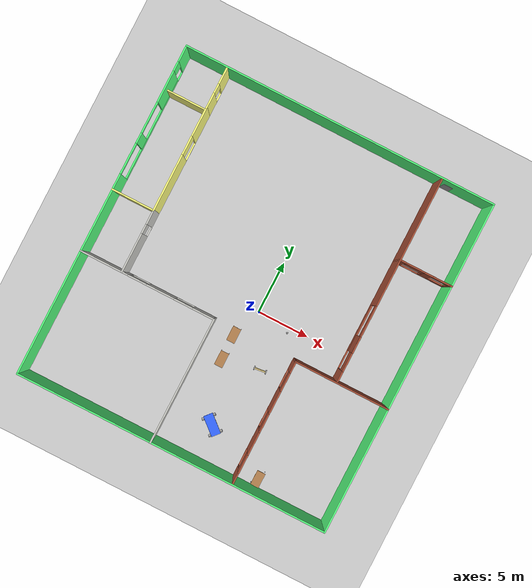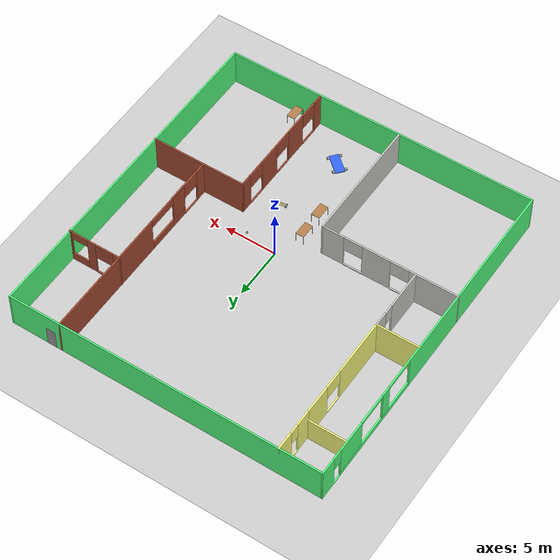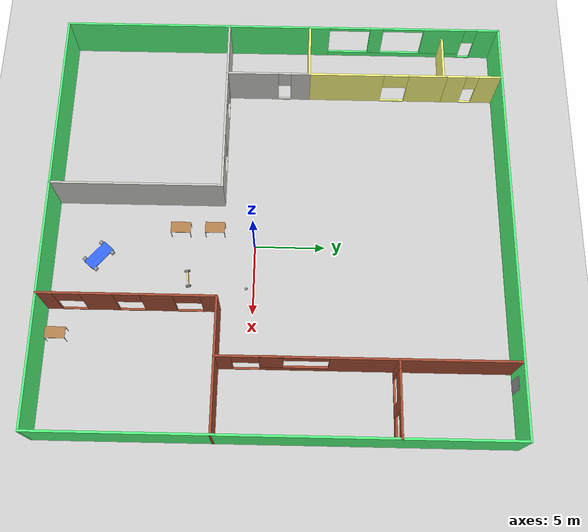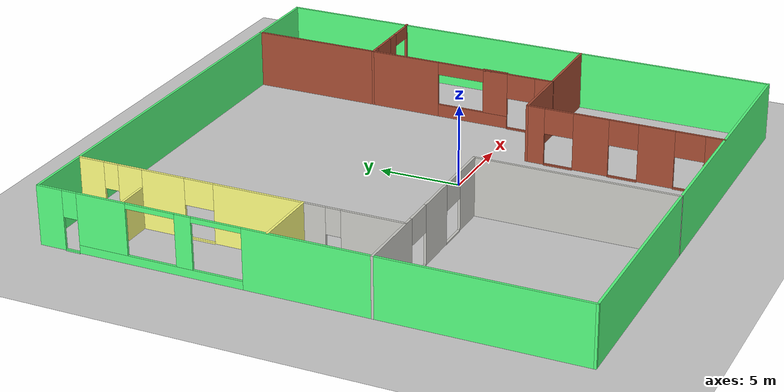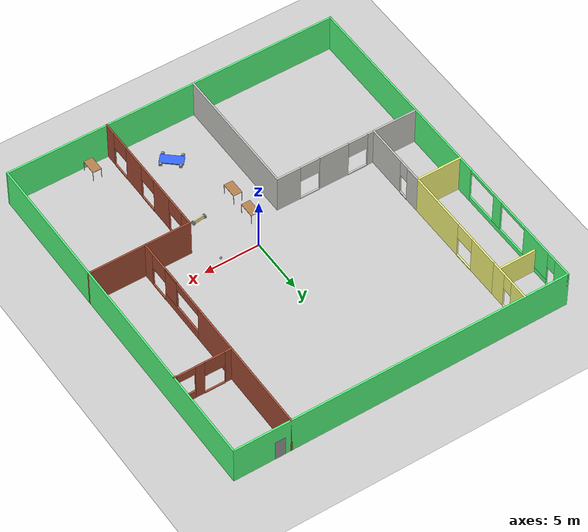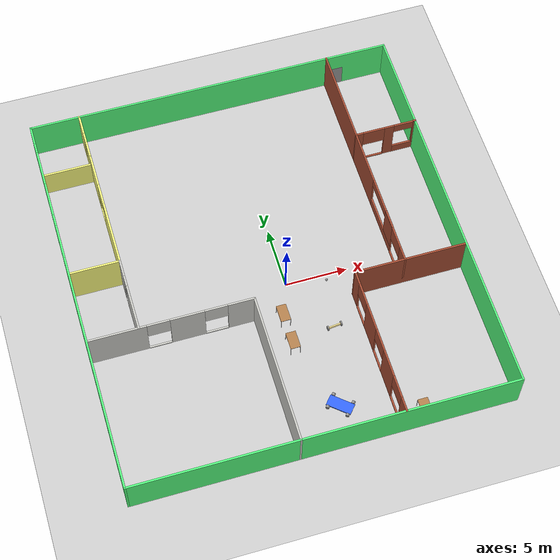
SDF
<sdf version="1.6">
 <world name="default">
  <plugin name="Project1" filename="libProject1.so"/>
  <light name="sun" type="directional">
   <pose>0 0 10 0 -0 0</pose>
   <diffuse>0.8 0.8 0.8 1</diffuse>
   <specular>0.1 0.1 0.1 1</specular>
   <attenuation>
    <range>1000</range>
    <constant>0.9</constant>
    <linear>0.01</linear>
    <quadratic>0.001</quadratic>
   </attenuation>
   <direction>-0.5 0.5 -1</direction>
  </light>
  <model name="ground_plane">
   <static>1</static>
   <link name="link">
    <collision name="collision">
     <geometry><plane><normal>0 0 1</normal><size>100 100</size></plane></geometry>
     <surface><friction><ode><mu>100</mu><mu2>50</mu2></ode></friction></surface>
    </collision>
    <visual name="visual">
     <cast_shadows>0</cast_shadows>
     <geometry><plane><normal>0 0 1</normal><size>100 100</size></plane></geometry>
     <material>
      <script><uri>file://media/materials/scripts/gazebo.material</uri><name>Gazebo/Grey</name></script>
     </material>
    </visual>
   </link>
  </model>
  <gravity>0 0 -9.8</gravity>
  <magnetic_field>6e-06 2.3e-05 -4.2e-05</magnetic_field>
  <atmosphere type="adiabatic"/>
  <physics name="default_physics" default="0" type="ode">
   <max_step_size>0.001</max_step_size>
   <real_time_factor>1</real_time_factor>
   <real_time_update_rate>1000</real_time_update_rate>
  </physics>
  <scene><ambient>0.4 0.4 0.4 1</ambient><background>0.7 0.7 0.7 1</background><shadows>1</shadows></scene>
  <spherical_coordinates>
   <surface_model>EARTH_WGS84</surface_model>
   <latitude_deg>0</latitude_deg>
   <longitude_deg>0</longitude_deg>
   <elevation>0</elevation>
   <heading_deg>0</heading_deg>
  </spherical_coordinates>
  <model name="table_0">
   <static>0</static>
   <link name="link">
    <collision name="surface">
     <pose>0 0 1 0 -0 0</pose>
     <geometry><box><size>1.5 0.8 0.03</size></box></geometry>
     <surface><friction><ode><mu>0.6</mu><mu2>0.6</mu2></ode></friction></surface>
    </collision>
    <visual name="visual1">
     <pose>0 0 1 0 -0 0</pose>
     <geometry><box><size>1.4 0.8 0.04</size></box></geometry>
     <material>
      <script><uri>file://media/materials/scripts/gazebo.material</uri><name>Gazebo/Wood</name></script>
     </material>
    </visual>
    <collision name="front_left_leg">
     <pose>0.68 0.38 0.5 0 -0 0</pose>
     <geometry><cylinder><radius>0.02</radius><length>1</length></cylinder></geometry>
    </collision>
    <visual name="front_left_leg">
     <pose>0.68 0.38 0.5 0 -0 0</pose>
     <geometry><cylinder><radius>0.02</radius><length>1</length></cylinder></geometry>
     <material>
      <script><uri>file://media/materials/scripts/gazebo.material</uri><name>Gazebo/Grey</name></script>
     </material>
    </visual>
    <collision name="front_right_leg">
     <pose>0.68 -0.38 0.5 0 -0 0</pose>
     <geometry><cylinder><radius>0.02</radius><length>1</length></cylinder></geometry>
    </collision>
    <visual name="front_right_leg">
     <pose>0.68 -0.38 0.5 0 -0 0</pose>
     <geometry><cylinder><radius>0.02</radius><length>1</length></cylinder></geometry>
     <material>
      <script><uri>file://media/materials/scripts/gazebo.material</uri><name>Gazebo/Grey</name></script>
     </material>
    </visual>
    <collision name="back_right_leg">
     <pose>-0.68 -0.38 0.5 0 -0 0</pose>
     <geometry><cylinder><radius>0.02</radius><length>1</length></cylinder></geometry>
    </collision>
    <visual name="back_right_leg">
     <pose>-0.68 -0.38 0.5 0 -0 0</pose>
     <geometry><cylinder><radius>0.02</radius><length>1</length></cylinder></geometry>
     <material>
      <script><uri>file://media/materials/scripts/gazebo.material</uri><name>Gazebo/Grey</name></script>
     </material>
    </visual>
    <collision name="back_left_leg">
     <pose>-0.68 0.38 0.5 0 -0 0</pose>
     <geometry><cylinder><radius>0.02</radius><length>1</length></cylinder></geometry>
    </collision>
    <visual name="back_left_leg">
     <pose>-0.68 0.38 0.5 0 -0 0</pose>
     <geometry><cylinder><radius>0.02</radius><length>1</length></cylinder></geometry>
     <material>
      <script><uri>file://media/materials/scripts/gazebo.material</uri><name>Gazebo/Grey</name></script>
     </material>
    </visual>
    <inertial>
     <inertia><ixx>1</ixx><ixy>0</ixy><ixz>0</ixz><iyy>1</iyy><iyz>0</iyz><izz>1</izz></inertia>
     <mass>1</mass>
    </inertial>
   </link>
   <pose>6.803 -13.3459 -3e-06 -2e-06 -2e-06 1.57</pose>
  </model>
  <model name="table_3_clone_clone_clone_0">
   <static>0</static>
   <link name="link">
    <collision name="surface">
     <pose>0 0 1 0 -0 0</pose>
     <geometry><box><size>1.5 0.8 0.03</size></box></geometry>
     <surface><friction><ode><mu>0.6</mu><mu2>0.6</mu2></ode></friction></surface>
    </collision>
    <visual name="visual1">
     <pose>0 0 1 0 -0 0</pose>
     <geometry><box><size>1.4 0.8 0.04</size></box></geometry>
     <material>
      <script><uri>file://media/materials/scripts/gazebo.material</uri><name>Gazebo/Wood</name></script>
     </material>
    </visual>
    <collision name="front_left_leg">
     <pose>0.68 0.38 0.5 0 -0 0</pose>
     <geometry><cylinder><radius>0.02</radius><length>1</length></cylinder></geometry>
    </collision>
    <visual name="front_left_leg">
     <pose>0.68 0.38 0.5 0 -0 0</pose>
     <geometry><cylinder><radius>0.02</radius><length>1</length></cylinder></geometry>
     <material>
      <script><uri>file://media/materials/scripts/gazebo.material</uri><name>Gazebo/Grey</name></script>
     </material>
    </visual>
    <collision name="front_right_leg">
     <pose>0.68 -0.38 0.5 0 -0 0</pose>
     <geometry><cylinder><radius>0.02</radius><length>1</length></cylinder></geometry>
    </collision>
    <visual name="front_right_leg">
     <pose>0.68 -0.38 0.5 0 -0 0</pose>
     <geometry><cylinder><radius>0.02</radius><length>1</length></cylinder></geometry>
     <material>
      <script><uri>file://media/materials/scripts/gazebo.material</uri><name>Gazebo/Grey</name></script>
     </material>
    </visual>
    <collision name="back_right_leg">
     <pose>-0.68 -0.38 0.5 0 -0 0</pose>
     <geometry><cylinder><radius>0.02</radius><length>1</length></cylinder></geometry>
    </collision>
    <visual name="back_right_leg">
     <pose>-0.68 -0.38 0.5 0 -0 0</pose>
     <geometry><cylinder><radius>0.02</radius><length>1</length></cylinder></geometry>
     <material>
      <script><uri>file://media/materials/scripts/gazebo.material</uri><name>Gazebo/Grey</name></script>
     </material>
    </visual>
    <collision name="back_left_leg">
     <pose>-0.68 0.38 0.5 0 -0 0</pose>
     <geometry><cylinder><radius>0.02</radius><length>1</length></cylinder></geometry>
    </collision>
    <visual name="back_left_leg">
     <pose>-0.68 0.38 0.5 0 -0 0</pose>
     <geometry><cylinder><radius>0.02</radius><length>1</length></cylinder></geometry>
     <material>
      <script><uri>file://media/materials/scripts/gazebo.material</uri><name>Gazebo/Grey</name></script>
     </material>
    </visual>
    <inertial>
     <inertia><ixx>1</ixx><ixy>0</ixy><ixz>0</ixz><iyy>1</iyy><iyz>0</iyz><izz>1</izz></inertia>
     <mass>1</mass>
    </inertial>
   </link>
   <pose>-1.06808 -2.82716 -0 0 -0 1.57001</pose>
  </model>
  <model name="table_3_clone_clone_clone_0_clone">
   <static>0</static>
   <link name="link">
    <collision name="surface">
     <pose>0 0 1 0 -0 0</pose>
     <geometry><box><size>1.5 0.8 0.03</size></box></geometry>
     <surface><friction><ode><mu>0.6</mu><mu2>0.6</mu2></ode></friction></surface>
    </collision>
    <visual name="visual1">
     <pose>0 0 1 0 -0 0</pose>
     <geometry><box><size>1.4 0.8 0.04</size></box></geometry>
     <material>
      <script><uri>file://media/materials/scripts/gazebo.material</uri><name>Gazebo/Wood</name></script>
     </material>
    </visual>
    <collision name="front_left_leg">
     <pose>0.68 0.38 0.5 0 -0 0</pose>
     <geometry><cylinder><radius>0.02</radius><length>1</length></cylinder></geometry>
    </collision>
    <visual name="front_left_leg">
     <pose>0.68 0.38 0.5 0 -0 0</pose>
     <geometry><cylinder><radius>0.02</radius><length>1</length></cylinder></geometry>
     <material>
      <script><uri>file://media/materials/scripts/gazebo.material</uri><name>Gazebo/Grey</name></script>
     </material>
    </visual>
    <collision name="front_right_leg">
     <pose>0.68 -0.38 0.5 0 -0 0</pose>
     <geometry><cylinder><radius>0.02</radius><length>1</length></cylinder></geometry>
    </collision>
    <visual name="front_right_leg">
     <pose>0.68 -0.38 0.5 0 -0 0</pose>
     <geometry><cylinder><radius>0.02</radius><length>1</length></cylinder></geometry>
     <material>
      <script><uri>file://media/materials/scripts/gazebo.material</uri><name>Gazebo/Grey</name></script>
     </material>
    </visual>
    <collision name="back_right_leg">
     <pose>-0.68 -0.38 0.5 0 -0 0</pose>
     <geometry><cylinder><radius>0.02</radius><length>1</length></cylinder></geometry>
    </collision>
    <visual name="back_right_leg">
     <pose>-0.68 -0.38 0.5 0 -0 0</pose>
     <geometry><cylinder><radius>0.02</radius><length>1</length></cylinder></geometry>
     <material>
      <script><uri>file://media/materials/scripts/gazebo.material</uri><name>Gazebo/Grey</name></script>
     </material>
    </visual>
    <collision name="back_left_leg">
     <pose>-0.68 0.38 0.5 0 -0 0</pose>
     <geometry><cylinder><radius>0.02</radius><length>1</length></cylinder></geometry>
    </collision>
    <visual name="back_left_leg">
     <pose>-0.68 0.38 0.5 0 -0 0</pose>
     <geometry><cylinder><radius>0.02</radius><length>1</length></cylinder></geometry>
     <material>
      <script><uri>file://media/materials/scripts/gazebo.material</uri><name>Gazebo/Grey</name></script>
     </material>
    </visual>
    <inertial>
     <inertia><ixx>1</ixx><ixy>0</ixy><ixz>0</ixz><iyy>1</iyy><iyz>0</iyz><izz>1</izz></inertia>
     <mass>1</mass>
    </inertial>
   </link>
   <pose>-1.03399 -5.26338 -0 0 -0 1.57001</pose>
  </model>
  <model name="robot_0">
   <link name="link_0">
    <inertial>
     <mass>1.59387</mass>
     <inertia>
      <ixx>0.470249</ixx>
      <ixy>0</ixy>
      <ixz>0</ixz>
      <iyy>0.265646</iyy>
      <iyz>0</iyz>
      <izz>0.470249</izz>
     </inertia>
    </inertial>
    <visual name="visual">
     <geometry><box><size>0.3 1 0.1</size></box></geometry>
     <material>
      <lighting>1</lighting>
      <script><uri>file://media/materials/scripts/gazebo.material</uri><name>Gazebo/Grey</name></script>
      <ambient>1 0.9 0.6 1</ambient>
      <diffuse>1 0.9 0.6 1</diffuse>
      <specular>0.01 0.01 0.01 1</specular>
      <emissive>0 0 0 1</emissive>
      <shader type="vertex"><normal_map>__default__</normal_map></shader>
     </material>
    </visual>
    <collision name="collision">
     <geometry><box><size>0.3 1 0.1</size></box></geometry>
     <surface>
      <friction>
       <ode><mu>1</mu><mu2>1</mu2><fdir1>0 0 0</fdir1><slip1>0</slip1><slip2>0</slip2></ode>
       <torsional>
        <coefficient>1</coefficient>
        <patch_radius>0</patch_radius>
        <surface_radius>0</surface_radius>
        <use_patch_radius>1</use_patch_radius>
        <ode><slip>0</slip></ode>
       </torsional>
      </friction>
      <bounce><restitution_coefficient>0</restitution_coefficient><threshold>1e+06</threshold></bounce>
      <contact>
       <collide_without_contact>0</collide_without_contact>
       <collide_without_contact_bitmask>1</collide_without_contact_bitmask>
       <collide_bitmask>1</collide_bitmask>
       <ode>
        <soft_cfm>0</soft_cfm>
        <soft_erp>0.2</soft_erp>
        <kp>1e+13</kp>
        <kd>1</kd>
        <max_vel>0.01</max_vel>
        <min_depth>0</min_depth>
       </ode>
       <bullet>
        <split_impulse>1</split_impulse>
        <split_impulse_penetration_threshold>-0.01</split_impulse_penetration_threshold>
        <soft_cfm>0</soft_cfm>
        <soft_erp>0.2</soft_erp>
        <kp>1e+13</kp>
        <kd>1</kd>
       </bullet>
      </contact>
     </surface>
    </collision>
   </link>
   <link name="link_1">
    <pose>0 -0.550019 -0 1.5707 -0 0</pose>
    <inertial>
     <mass>1</mass>
     <inertia><ixx>0.145833</ixx><ixy>0</ixy><ixz>0</ixz><iyy>0.145833</iyy><iyz>0</iyz><izz>0.125</izz></inertia>
    </inertial>
    <visual name="visual">
     <geometry><cylinder><radius>0.2</radius><length>0.1</length></cylinder></geometry>
     <material>
      <lighting>1</lighting>
      <script><uri>file://media/materials/scripts/gazebo.material</uri><name>Gazebo/Grey</name></script>
      <ambient>0.5 0.5 0.5 1</ambient>
      <diffuse>0.5 0.5 0.5 1</diffuse>
      <specular>0.01 0.01 0.01 1</specular>
      <emissive>0 0 0 1</emissive>
      <shader type="vertex"><normal_map>__default__</normal_map></shader>
     </material>
    </visual>
    <collision name="collision">
     <geometry><cylinder><radius>0.2</radius><length>0.1</length></cylinder></geometry>
     <surface>
      <friction>
       <ode><mu>1</mu><mu2>1</mu2><fdir1>0 0 0</fdir1><slip1>0</slip1><slip2>0</slip2></ode>
       <torsional>
        <coefficient>1</coefficient>
        <patch_radius>0</patch_radius>
        <surface_radius>0</surface_radius>
        <use_patch_radius>1</use_patch_radius>
        <ode><slip>0</slip></ode>
       </torsional>
      </friction>
      <bounce><restitution_coefficient>0</restitution_coefficient><threshold>1e+06</threshold></bounce>
      <contact>
       <collide_without_contact>0</collide_without_contact>
       <collide_without_contact_bitmask>1</collide_without_contact_bitmask>
       <collide_bitmask>1</collide_bitmask>
       <ode>
        <soft_cfm>0</soft_cfm>
        <soft_erp>0.2</soft_erp>
        <kp>1e+13</kp>
        <kd>1</kd>
        <max_vel>0.01</max_vel>
        <min_depth>0</min_depth>
       </ode>
       <bullet>
        <split_impulse>1</split_impulse>
        <split_impulse_penetration_threshold>-0.01</split_impulse_penetration_threshold>
        <soft_cfm>0</soft_cfm>
        <soft_erp>0.2</soft_erp>
        <kp>1e+13</kp>
        <kd>1</kd>
       </bullet>
      </contact>
     </surface>
    </collision>
   </link>
   <link name="link_1_clone">
    <pose>-0 0.550019 0 1.5707 -0 0</pose>
    <inertial>
     <mass>1</mass>
     <inertia><ixx>0.145833</ixx><ixy>0</ixy><ixz>0</ixz><iyy>0.145833</iyy><iyz>0</iyz><izz>0.125</izz></inertia>
    </inertial>
    <visual name="visual">
     <geometry><cylinder><radius>0.2</radius><length>0.1</length></cylinder></geometry>
     <material>
      <lighting>1</lighting>
      <script><uri>file://media/materials/scripts/gazebo.material</uri><name>Gazebo/Grey</name></script>
      <ambient>0.5 0.5 0.5 1</ambient>
      <diffuse>0.5 0.5 0.5 1</diffuse>
      <specular>0.01 0.01 0.01 1</specular>
      <emissive>0 0 0 1</emissive>
      <shader type="vertex"><normal_map>__default__</normal_map></shader>
     </material>
    </visual>
    <collision name="collision">
     <geometry><cylinder><radius>0.2</radius><length>0.1</length></cylinder></geometry>
     <surface>
      <friction>
       <ode><mu>1</mu><mu2>1</mu2><fdir1>0 0 0</fdir1><slip1>0</slip1><slip2>0</slip2></ode>
       <torsional>
        <coefficient>1</coefficient>
        <patch_radius>0</patch_radius>
        <surface_radius>0</surface_radius>
        <use_patch_radius>1</use_patch_radius>
        <ode><slip>0</slip></ode>
       </torsional>
      </friction>
      <bounce><restitution_coefficient>0</restitution_coefficient><threshold>1e+06</threshold></bounce>
      <contact>
       <collide_without_contact>0</collide_without_contact>
       <collide_without_contact_bitmask>1</collide_without_contact_bitmask>
       <collide_bitmask>1</collide_bitmask>
       <ode>
        <soft_cfm>0</soft_cfm>
        <soft_erp>0.2</soft_erp>
        <kp>1e+13</kp>
        <kd>1</kd>
        <max_vel>0.01</max_vel>
        <min_depth>0</min_depth>
       </ode>
       <bullet>
        <split_impulse>1</split_impulse>
        <split_impulse_penetration_threshold>-0.01</split_impulse_penetration_threshold>
        <soft_cfm>0</soft_cfm>
        <soft_erp>0.2</soft_erp>
        <kp>1e+13</kp>
        <kd>1</kd>
       </bullet>
      </contact>
     </surface>
    </collision>
   </link>
   <joint name="link_0_JOINT_0" type="revolute">
    <parent>link_0</parent>
    <child>link_1</child>
    <axis>
     <xyz>0 0 1</xyz>
     <use_parent_model_frame>0</use_parent_model_frame>
     <limit>
      <lower>-1.79769e+308</lower>
      <upper>1.79769e+308</upper>
      <effort>-1</effort>
      <velocity>-1</velocity>
     </limit>
     <dynamics>
      <spring_reference>0</spring_reference>
      <spring_stiffness>0</spring_stiffness>
      <damping>0</damping>
      <friction>0</friction>
     </dynamics>
    </axis>
    <physics>
     <ode><limit><cfm>0</cfm><erp>0.2</erp></limit><suspension><cfm>0</cfm><erp>0.2</erp></suspension></ode>
    </physics>
   </joint>
   <joint name="link_0_JOINT_1" type="revolute">
    <parent>link_0</parent>
    <child>link_1_clone</child>
    <axis>
     <xyz>0 0 1</xyz>
     <use_parent_model_frame>0</use_parent_model_frame>
     <limit>
      <lower>-1.79769e+308</lower>
      <upper>1.79769e+308</upper>
      <effort>-1</effort>
      <velocity>-1</velocity>
     </limit>
     <dynamics>
      <spring_reference>0</spring_reference>
      <spring_stiffness>0</spring_stiffness>
      <damping>0</damping>
      <friction>0</friction>
     </dynamics>
    </axis>
    <physics>
     <ode><limit><cfm>0</cfm><erp>0.2</erp></limit><suspension><cfm>0</cfm><erp>0.2</erp></suspension></ode>
    </physics>
   </joint>
   <static>0</static>
   <pose>2.52428 -4.62436 0.199992 -3.14157 -1.4352 -1.46064</pose>
  </model>
  <model name="gokart_3">
   <link name="link_0">
    <pose>1e-06 -0.118472 -0 -0 -0 -0</pose>
    <inertial>
     <mass>1.59387</mass>
     <inertia>
      <ixx>0.470249</ixx>
      <ixy>0</ixy>
      <ixz>0</ixz>
      <iyy>0.265646</iyy>
      <iyz>0</iyz>
      <izz>0.470249</izz>
     </inertia>
    </inertial>
    <visual name="visual">
     <geometry><box><size>2 0.9 0.1</size></box></geometry>
     <material>
      <lighting>1</lighting>
      <script><uri>file://media/materials/scripts/gazebo.material</uri><name>Gazebo/Grey</name></script>
      <ambient>0.2 0.4 1 1</ambient>
      <diffuse>0.2 0.4 1 1</diffuse>
      <specular>0.01 0.01 0.01 1</specular>
      <emissive>0 0 0 1</emissive>
      <shader type="vertex"><normal_map>__default__</normal_map></shader>
     </material>
    </visual>
    <collision name="collision">
     <geometry><box><size>2 0.9 0.1</size></box></geometry>
     <surface>
      <friction>
       <ode><mu>1</mu><mu2>1</mu2><fdir1>0 0 0</fdir1><slip1>0</slip1><slip2>0</slip2></ode>
       <torsional>
        <coefficient>1</coefficient>
        <patch_radius>0</patch_radius>
        <surface_radius>0</surface_radius>
        <use_patch_radius>1</use_patch_radius>
        <ode><slip>0</slip></ode>
       </torsional>
      </friction>
      <bounce><restitution_coefficient>0</restitution_coefficient><threshold>1e+06</threshold></bounce>
      <contact>
       <collide_without_contact>0</collide_without_contact>
       <collide_without_contact_bitmask>1</collide_without_contact_bitmask>
       <collide_bitmask>1</collide_bitmask>
       <ode>
        <soft_cfm>0</soft_cfm>
        <soft_erp>0.2</soft_erp>
        <kp>1e+13</kp>
        <kd>1</kd>
        <max_vel>0.01</max_vel>
        <min_depth>0</min_depth>
       </ode>
       <bullet>
        <split_impulse>1</split_impulse>
        <split_impulse_penetration_threshold>-0.01</split_impulse_penetration_threshold>
        <soft_cfm>0</soft_cfm>
        <soft_erp>0.2</soft_erp>
        <kp>1e+13</kp>
        <kd>1</kd>
       </bullet>
      </contact>
     </surface>
    </collision>
   </link>
   <link name="link_1">
    <pose>-0.81362 -0.678506 9e-06 1.5707 -0 0</pose>
    <inertial>
     <mass>1</mass>
     <inertia><ixx>0.145833</ixx><ixy>0</ixy><ixz>0</ixz><iyy>0.145833</iyy><iyz>0</iyz><izz>0.125</izz></inertia>
    </inertial>
    <visual name="visual">
     <geometry><cylinder><radius>0.14</radius><length>0.22</length></cylinder></geometry>
     <material>
      <lighting>1</lighting>
      <script><uri>file://media/materials/scripts/gazebo.material</uri><name>Gazebo/Grey</name></script>
      <ambient>0.1 0.1 0.1 1</ambient>
      <diffuse>0.1 0.1 0.1 1</diffuse>
      <specular>0.01 0.01 0.01 1</specular>
      <emissive>0 0 0 1</emissive>
      <shader type="vertex"><normal_map>__default__</normal_map></shader>
     </material>
    </visual>
    <collision name="collision">
     <geometry><cylinder><radius>0.14</radius><length>0.22</length></cylinder></geometry>
     <surface>
      <friction>
       <ode><mu>1</mu><mu2>1</mu2><fdir1>0 0 0</fdir1><slip1>0</slip1><slip2>0</slip2></ode>
       <torsional>
        <coefficient>1</coefficient>
        <patch_radius>0</patch_radius>
        <surface_radius>0</surface_radius>
        <use_patch_radius>1</use_patch_radius>
        <ode><slip>0</slip></ode>
       </torsional>
      </friction>
      <bounce><restitution_coefficient>0</restitution_coefficient><threshold>1e+06</threshold></bounce>
      <contact>
       <collide_without_contact>0</collide_without_contact>
       <collide_without_contact_bitmask>1</collide_without_contact_bitmask>
       <collide_bitmask>1</collide_bitmask>
       <ode>
        <soft_cfm>0</soft_cfm>
        <soft_erp>0.2</soft_erp>
        <kp>1e+13</kp>
        <kd>1</kd>
        <max_vel>0.01</max_vel>
        <min_depth>0</min_depth>
       </ode>
       <bullet>
        <split_impulse>1</split_impulse>
        <split_impulse_penetration_threshold>-0.01</split_impulse_penetration_threshold>
        <soft_cfm>0</soft_cfm>
        <soft_erp>0.2</soft_erp>
        <kp>1e+13</kp>
        <kd>1</kd>
       </bullet>
      </contact>
     </surface>
    </collision>
   </link>
   <link name="link_1_clone">
    <pose>-0.813633 0.441545 0 1.5707 -0 0</pose>
    <inertial>
     <mass>1</mass>
     <inertia><ixx>0.145833</ixx><ixy>0</ixy><ixz>0</ixz><iyy>0.145833</iyy><iyz>0</iyz><izz>0.125</izz></inertia>
    </inertial>
    <visual name="visual">
     <geometry><cylinder><radius>0.14</radius><length>0.22</length></cylinder></geometry>
     <material>
      <lighting>1</lighting>
      <script><uri>file://media/materials/scripts/gazebo.material</uri><name>Gazebo/Grey</name></script>
      <ambient>0.1 0.1 0.1 1</ambient>
      <diffuse>0.1 0.1 0.1 1</diffuse>
      <specular>0.01 0.01 0.01 1</specular>
      <emissive>0 0 0 1</emissive>
      <shader type="vertex"><normal_map>__default__</normal_map></shader>
     </material>
    </visual>
    <collision name="collision">
     <geometry><cylinder><radius>0.14</radius><length>0.22</length></cylinder></geometry>
     <surface>
      <friction>
       <ode><mu>1</mu><mu2>1</mu2><fdir1>0 0 0</fdir1><slip1>0</slip1><slip2>0</slip2></ode>
       <torsional>
        <coefficient>1</coefficient>
        <patch_radius>0</patch_radius>
        <surface_radius>0</surface_radius>
        <use_patch_radius>1</use_patch_radius>
        <ode><slip>0</slip></ode>
       </torsional>
      </friction>
      <bounce><restitution_coefficient>0</restitution_coefficient><threshold>1e+06</threshold></bounce>
      <contact>
       <collide_without_contact>0</collide_without_contact>
       <collide_without_contact_bitmask>1</collide_without_contact_bitmask>
       <collide_bitmask>1</collide_bitmask>
       <ode>
        <soft_cfm>0</soft_cfm>
        <soft_erp>0.2</soft_erp>
        <kp>1e+13</kp>
        <kd>1</kd>
        <max_vel>0.01</max_vel>
        <min_depth>0</min_depth>
       </ode>
       <bullet>
        <split_impulse>1</split_impulse>
        <split_impulse_penetration_threshold>-0.01</split_impulse_penetration_threshold>
        <soft_cfm>0</soft_cfm>
        <soft_erp>0.2</soft_erp>
        <kp>1e+13</kp>
        <kd>1</kd>
       </bullet>
      </contact>
     </surface>
    </collision>
   </link>
   <link name="link_1_clone_0">
    <pose>0.8 -0.678488 6e-06 1.5707 1.1e-05 1.1e-05</pose>
    <inertial>
     <mass>1</mass>
     <inertia><ixx>0.145833</ixx><ixy>0</ixy><ixz>0</ixz><iyy>0.145833</iyy><iyz>0</iyz><izz>0.125</izz></inertia>
    </inertial>
    <visual name="visual">
     <geometry><cylinder><radius>0.14</radius><length>0.22</length></cylinder></geometry>
     <material>
      <lighting>1</lighting>
      <script><uri>file://media/materials/scripts/gazebo.material</uri><name>Gazebo/Grey</name></script>
      <ambient>0.1 0.1 0.1 1</ambient>
      <diffuse>0.1 0.1 0.1 1</diffuse>
      <specular>0.01 0.01 0.01 1</specular>
      <emissive>0 0 0 1</emissive>
      <shader type="vertex"><normal_map>__default__</normal_map></shader>
     </material>
    </visual>
    <collision name="collision">
     <geometry><cylinder><radius>0.14</radius><length>0.22</length></cylinder></geometry>
     <surface>
      <friction>
       <ode><mu>1</mu><mu2>1</mu2><fdir1>0 0 0</fdir1><slip1>0</slip1><slip2>0</slip2></ode>
       <torsional>
        <coefficient>1</coefficient>
        <patch_radius>0</patch_radius>
        <surface_radius>0</surface_radius>
        <use_patch_radius>1</use_patch_radius>
        <ode><slip>0</slip></ode>
       </torsional>
      </friction>
      <bounce><restitution_coefficient>0</restitution_coefficient><threshold>1e+06</threshold></bounce>
      <contact>
       <collide_without_contact>0</collide_without_contact>
       <collide_without_contact_bitmask>1</collide_without_contact_bitmask>
       <collide_bitmask>1</collide_bitmask>
       <ode>
        <soft_cfm>0</soft_cfm>
        <soft_erp>0.2</soft_erp>
        <kp>1e+13</kp>
        <kd>1</kd>
        <max_vel>0.01</max_vel>
        <min_depth>0</min_depth>
       </ode>
       <bullet>
        <split_impulse>1</split_impulse>
        <split_impulse_penetration_threshold>-0.01</split_impulse_penetration_threshold>
        <soft_cfm>0</soft_cfm>
        <soft_erp>0.2</soft_erp>
        <kp>1e+13</kp>
        <kd>1</kd>
       </bullet>
      </contact>
     </surface>
    </collision>
   </link>
   <link name="link_1_clone_1">
    <pose>0.800005 0.441562 -2e-06 1.5707 1.1e-05 1.1e-05</pose>
    <inertial>
     <mass>1</mass>
     <inertia><ixx>0.145833</ixx><ixy>0</ixy><ixz>0</ixz><iyy>0.145833</iyy><iyz>0</iyz><izz>0.125</izz></inertia>
    </inertial>
    <visual name="visual">
     <geometry><cylinder><radius>0.14</radius><length>0.22</length></cylinder></geometry>
     <material>
      <lighting>1</lighting>
      <script><uri>file://media/materials/scripts/gazebo.material</uri><name>Gazebo/Grey</name></script>
      <ambient>0.1 0.1 0.1 1</ambient>
      <diffuse>0.1 0.1 0.1 1</diffuse>
      <specular>0.01 0.01 0.01 1</specular>
      <emissive>0 0 0 1</emissive>
      <shader type="vertex"><normal_map>__default__</normal_map></shader>
     </material>
    </visual>
    <collision name="collision">
     <geometry><cylinder><radius>0.14</radius><length>0.22</length></cylinder></geometry>
     <surface>
      <friction>
       <ode><mu>1</mu><mu2>1</mu2><fdir1>0 0 0</fdir1><slip1>0</slip1><slip2>0</slip2></ode>
       <torsional>
        <coefficient>1</coefficient>
        <patch_radius>0</patch_radius>
        <surface_radius>0</surface_radius>
        <use_patch_radius>1</use_patch_radius>
        <ode><slip>0</slip></ode>
       </torsional>
      </friction>
      <bounce><restitution_coefficient>0</restitution_coefficient><threshold>1e+06</threshold></bounce>
      <contact>
       <collide_without_contact>0</collide_without_contact>
       <collide_without_contact_bitmask>1</collide_without_contact_bitmask>
       <collide_bitmask>1</collide_bitmask>
       <ode>
        <soft_cfm>0</soft_cfm>
        <soft_erp>0.2</soft_erp>
        <kp>1e+13</kp>
        <kd>1</kd>
        <max_vel>0.01</max_vel>
        <min_depth>0</min_depth>
       </ode>
       <bullet>
        <split_impulse>1</split_impulse>
        <split_impulse_penetration_threshold>-0.01</split_impulse_penetration_threshold>
        <soft_cfm>0</soft_cfm>
        <soft_erp>0.2</soft_erp>
        <kp>1e+13</kp>
        <kd>1</kd>
       </bullet>
      </contact>
     </surface>
    </collision>
   </link>
   <joint name="link_0_JOINT_0_0" type="revolute">
    <parent>link_0</parent>
    <child>link_1_clone_0</child>
    <axis>
     <xyz>0 0 1</xyz>
     <use_parent_model_frame>0</use_parent_model_frame>
     <limit>
      <lower>-1.79769e+308</lower>
      <upper>1.79769e+308</upper>
      <effort>-1</effort>
      <velocity>-1</velocity>
     </limit>
     <dynamics>
      <spring_reference>0</spring_reference>
      <spring_stiffness>0</spring_stiffness>
      <damping>0</damping>
      <friction>0</friction>
     </dynamics>
    </axis>
    <physics>
     <ode><limit><cfm>0</cfm><erp>0.2</erp></limit><suspension><cfm>0</cfm><erp>0.2</erp></suspension></ode>
    </physics>
   </joint>
   <joint name="link_0_JOINT_0" type="revolute">
    <parent>link_0</parent>
    <child>link_1</child>
    <axis>
     <xyz>0 0 1</xyz>
     <use_parent_model_frame>0</use_parent_model_frame>
     <limit>
      <lower>-1.79769e+308</lower>
      <upper>1.79769e+308</upper>
      <effort>-1</effort>
      <velocity>-1</velocity>
     </limit>
     <dynamics>
      <spring_reference>0</spring_reference>
      <spring_stiffness>0</spring_stiffness>
      <damping>0</damping>
      <friction>0</friction>
     </dynamics>
    </axis>
    <physics>
     <ode><limit><cfm>0</cfm><erp>0.2</erp></limit><suspension><cfm>0</cfm><erp>0.2</erp></suspension></ode>
    </physics>
   </joint>
   <joint name="link_0_JOINT_1_0" type="revolute">
    <parent>link_0</parent>
    <child>link_1_clone_1</child>
    <axis>
     <xyz>1 0 0</xyz>
     <use_parent_model_frame>0</use_parent_model_frame>
     <limit>
      <lower>-1.79769e+308</lower>
      <upper>1.79769e+308</upper>
      <effort>-1</effort>
      <velocity>-1</velocity>
     </limit>
     <dynamics>
      <spring_reference>0</spring_reference>
      <spring_stiffness>0</spring_stiffness>
      <damping>0</damping>
      <friction>0</friction>
     </dynamics>
    </axis>
    <physics>
     <ode><limit><cfm>0</cfm><erp>0.2</erp></limit><suspension><cfm>0</cfm><erp>0.2</erp></suspension></ode>
    </physics>
   </joint>
   <joint name="link_0_JOINT_1" type="revolute">
    <parent>link_0</parent>
    <child>link_1_clone</child>
    <axis>
     <xyz>0 0 1</xyz>
     <use_parent_model_frame>0</use_parent_model_frame>
     <limit>
      <lower>-1.79769e+308</lower>
      <upper>1.79769e+308</upper>
      <effort>-1</effort>
      <velocity>-1</velocity>
     </limit>
     <dynamics>
      <spring_reference>0</spring_reference>
      <spring_stiffness>0</spring_stiffness>
      <damping>0</damping>
      <friction>0</friction>
     </dynamics>
    </axis>
    <physics>
     <ode><limit><cfm>0</cfm><erp>0.2</erp></limit><suspension><cfm>0</cfm><erp>0.2</erp></suspension></ode>
    </physics>
   </joint>
   <static>0</static>
   <pose>0.859445 -11.1412 0.140008 8e-06 -2e-06 2.43327</pose>
  </model>
  <model name="my_ball">
   <link name="link_0">
    <inertial>
     <mass>1</mass>
     <inertia><ixx>0.1</ixx><ixy>0</ixy><ixz>0</ixz><iyy>0.1</iyy><iyz>0</iyz><izz>0.1</izz></inertia>
    </inertial>
    <visual name="visual">
     <geometry><sphere><radius>0.1</radius></sphere></geometry>
     <material>
      <lighting>1</lighting>
      <script><uri>file://media/materials/scripts/gazebo.material</uri><name>Gazebo/Grey</name></script>
      <ambient>1 1 1 1</ambient>
      <diffuse>1 1 1 1</diffuse>
      <specular>1 1 1 1</specular>
      <emissive>1 1 1 1</emissive>
      <shader type="vertex"><normal_map>__default__</normal_map></shader>
     </material>
    </visual>
    <collision name="collision">
     <geometry><sphere><radius>0.1</radius></sphere></geometry>
     <surface>
      <friction>
       <ode><mu>1</mu><mu2>1</mu2><fdir1>0 0 0</fdir1><slip1>0</slip1><slip2>0</slip2></ode>
       <torsional>
        <coefficient>1</coefficient>
        <patch_radius>0</patch_radius>
        <surface_radius>0</surface_radius>
        <use_patch_radius>1</use_patch_radius>
        <ode><slip>0</slip></ode>
       </torsional>
      </friction>
      <bounce><restitution_coefficient>0</restitution_coefficient><threshold>1e+06</threshold></bounce>
      <contact>
       <collide_without_contact>0</collide_without_contact>
       <collide_without_contact_bitmask>1</collide_without_contact_bitmask>
       <collide_bitmask>1</collide_bitmask>
       <ode>
        <soft_cfm>0</soft_cfm>
        <soft_erp>0.2</soft_erp>
        <kp>1e+13</kp>
        <kd>1</kd>
        <max_vel>0.01</max_vel>
        <min_depth>0</min_depth>
       </ode>
       <bullet>
        <split_impulse>1</split_impulse>
        <split_impulse_penetration_threshold>-0.01</split_impulse_penetration_threshold>
        <soft_cfm>0</soft_cfm>
        <soft_erp>0.2</soft_erp>
        <kp>1e+13</kp>
        <kd>1</kd>
       </bullet>
      </contact>
     </surface>
    </collision>
   </link>
   <static>0</static>
   <pose>3.17286 -0.504878 0.1 0 -0 0</pose>
  </model>
  <audio><device>default</device></audio>
  <model name="myfloorplan">
   <link name="Door_22">
    <pose>11 16 0 0 -0 0</pose>
    <visual name="Door_22_Visual">
     <pose>0 0 1 0 -0 0</pose>
     <geometry><box><size>0.9 0.17 2</size></box></geometry>
     <material>
      <script><uri>file://media/materials/scripts/gazebo.material</uri><name>Gazebo/Grey</name></script>
     </material>
    </visual>
    <collision name="Door_22_Collision">
     <pose>0 0 1 0 -0 0</pose>
     <geometry><box><size>0.9 0.17 2</size></box></geometry>
     <surface>
      <friction>
       <ode><mu>1</mu><mu2>1</mu2><fdir1>0 0 0</fdir1><slip1>0</slip1><slip2>0</slip2></ode>
       <torsional>
        <coefficient>1</coefficient>
        <patch_radius>0</patch_radius>
        <surface_radius>0</surface_radius>
        <use_patch_radius>1</use_patch_radius>
        <ode><slip>0</slip></ode>
       </torsional>
      </friction>
      <bounce><restitution_coefficient>0</restitution_coefficient><threshold>1e+06</threshold></bounce>
      <contact>
       <collide_without_contact>0</collide_without_contact>
       <collide_without_contact_bitmask>1</collide_without_contact_bitmask>
       <collide_bitmask>1</collide_bitmask>
       <ode>
        <soft_cfm>0</soft_cfm>
        <soft_erp>0.2</soft_erp>
        <kp>1e+13</kp>
        <kd>1</kd>
        <max_vel>0.01</max_vel>
        <min_depth>0</min_depth>
       </ode>
       <bullet>
        <split_impulse>1</split_impulse>
        <split_impulse_penetration_threshold>-0.01</split_impulse_penetration_threshold>
        <soft_cfm>0</soft_cfm>
        <soft_erp>0.2</soft_erp>
        <kp>1e+13</kp>
        <kd>1</kd>
       </bullet>
      </contact>
     </surface>
    </collision>
   </link>
   <link name="Wall_0">
    <pose>0 16 0 0 -0 0</pose>
    <visual name="Wall_0_Visual">
     <pose>0 0 1.8 0 -0 0</pose>
     <geometry><box><size>30.15 0.15 3.6</size></box></geometry>
     <material>
      <script><uri>file://media/materials/scripts/gazebo.material</uri><name>Gazebo/Grey</name></script>
      <ambient>0.333333 1 0.498039 1</ambient>
     </material>
    </visual>
    <collision name="Wall_0_Collision">
     <pose>0 0 1.8 0 -0 0</pose>
     <geometry><box><size>30.15 0.15 3.6</size></box></geometry>
     <surface>
      <friction>
       <ode><mu>1</mu><mu2>1</mu2><fdir1>0 0 0</fdir1><slip1>0</slip1><slip2>0</slip2></ode>
       <torsional>
        <coefficient>1</coefficient>
        <patch_radius>0</patch_radius>
        <surface_radius>0</surface_radius>
        <use_patch_radius>1</use_patch_radius>
        <ode><slip>0</slip></ode>
       </torsional>
      </friction>
      <bounce><restitution_coefficient>0</restitution_coefficient><threshold>1e+06</threshold></bounce>
      <contact>
       <collide_without_contact>0</collide_without_contact>
       <collide_without_contact_bitmask>1</collide_without_contact_bitmask>
       <collide_bitmask>1</collide_bitmask>
       <ode>
        <soft_cfm>0</soft_cfm>
        <soft_erp>0.2</soft_erp>
        <kp>1e+13</kp>
        <kd>1</kd>
        <max_vel>0.01</max_vel>
        <min_depth>0</min_depth>
       </ode>
       <bullet>
        <split_impulse>1</split_impulse>
        <split_impulse_penetration_threshold>-0.01</split_impulse_penetration_threshold>
        <soft_cfm>0</soft_cfm>
        <soft_erp>0.2</soft_erp>
        <kp>1e+13</kp>
        <kd>1</kd>
       </bullet>
      </contact>
     </surface>
    </collision>
   </link>
   <link name="Wall_15">
    <pose>-2 -10 0 0 0 -1.5708</pose>
    <visual name="Wall_15_Visual">
     <pose>0 0 1.8 0 -0 0</pose>
     <geometry><box><size>12.15 0.15 3.6</size></box></geometry>
     <material>
      <script><uri>file://media/materials/scripts/gazebo.material</uri><name>Gazebo/CeilingTiled</name></script>
      <ambient>1 1 0.498039 1</ambient>
     </material>
    </visual>
    <collision name="Wall_15_Collision">
     <pose>0 0 1.8 0 -0 0</pose>
     <geometry><box><size>12.15 0.15 3.6</size></box></geometry>
     <surface>
      <friction>
       <ode><mu>1</mu><mu2>1</mu2><fdir1>0 0 0</fdir1><slip1>0</slip1><slip2>0</slip2></ode>
       <torsional>
        <coefficient>1</coefficient>
        <patch_radius>0</patch_radius>
        <surface_radius>0</surface_radius>
        <use_patch_radius>1</use_patch_radius>
        <ode><slip>0</slip></ode>
       </torsional>
      </friction>
      <bounce><restitution_coefficient>0</restitution_coefficient><threshold>1e+06</threshold></bounce>
      <contact>
       <collide_without_contact>0</collide_without_contact>
       <collide_without_contact_bitmask>1</collide_without_contact_bitmask>
       <collide_bitmask>1</collide_bitmask>
       <ode>
        <soft_cfm>0</soft_cfm>
        <soft_erp>0.2</soft_erp>
        <kp>1e+13</kp>
        <kd>1</kd>
        <max_vel>0.01</max_vel>
        <min_depth>0</min_depth>
       </ode>
       <bullet>
        <split_impulse>1</split_impulse>
        <split_impulse_penetration_threshold>-0.01</split_impulse_penetration_threshold>
        <soft_cfm>0</soft_cfm>
        <soft_erp>0.2</soft_erp>
        <kp>1e+13</kp>
        <kd>1</kd>
       </bullet>
      </contact>
     </surface>
    </collision>
   </link>
   <link name="Wall_17">
    <pose>10.5 -4 0 0 -0 0</pose>
    <visual name="Wall_17_Visual">
     <pose>0 0 1.8 0 -0 0</pose>
     <geometry><box><size>9.15 0.15 3.6</size></box></geometry>
     <material>
      <script><uri>file://media/materials/scripts/gazebo.material</uri><name>Gazebo/Bricks</name></script>
      <ambient>0.333333 0.666667 1 1</ambient>
     </material>
    </visual>
    <collision name="Wall_17_Collision">
     <pose>0 0 1.8 0 -0 0</pose>
     <geometry><box><size>9.15 0.15 3.6</size></box></geometry>
     <surface>
      <friction>
       <ode><mu>1</mu><mu2>1</mu2><fdir1>0 0 0</fdir1><slip1>0</slip1><slip2>0</slip2></ode>
       <torsional>
        <coefficient>1</coefficient>
        <patch_radius>0</patch_radius>
        <surface_radius>0</surface_radius>
        <use_patch_radius>1</use_patch_radius>
        <ode><slip>0</slip></ode>
       </torsional>
      </friction>
      <bounce><restitution_coefficient>0</restitution_coefficient><threshold>1e+06</threshold></bounce>
      <contact>
       <collide_without_contact>0</collide_without_contact>
       <collide_without_contact_bitmask>1</collide_without_contact_bitmask>
       <collide_bitmask>1</collide_bitmask>
       <ode>
        <soft_cfm>0</soft_cfm>
        <soft_erp>0.2</soft_erp>
        <kp>1e+13</kp>
        <kd>1</kd>
        <max_vel>0.01</max_vel>
        <min_depth>0</min_depth>
       </ode>
       <bullet>
        <split_impulse>1</split_impulse>
        <split_impulse_penetration_threshold>-0.01</split_impulse_penetration_threshold>
        <soft_cfm>0</soft_cfm>
        <soft_erp>0.2</soft_erp>
        <kp>1e+13</kp>
        <kd>1</kd>
       </bullet>
      </contact>
     </surface>
    </collision>
   </link>
   <link name="Wall_23">
    <pose>10 6 0 0 0 -1.5708</pose>
    <visual name="Wall_23_Visual_0">
     <pose>-3.7875 0 1.8 0 -0 0</pose>
     <geometry><box><size>12.575 0.15 3.6</size></box></geometry>
     <material>
      <script><uri>file://media/materials/scripts/gazebo.material</uri><name>Gazebo/Bricks</name></script>
      <ambient>0.333333 0.666667 1 1</ambient>
     </material>
    </visual>
    <visual name="Wall_23_Visual_1">
     <pose>9.4875 0 1.8 0 -0 0</pose>
     <geometry><box><size>1.175 0.15 3.6</size></box></geometry>
     <material>
      <script><uri>file://media/materials/scripts/gazebo.material</uri><name>Gazebo/Bricks</name></script>
      <ambient>0.333333 0.666667 1 1</ambient>
     </material>
    </visual>
    <visual name="Wall_23_Visual_2">
     <pose>4.8 0 0.4 0 -0 0</pose>
     <geometry><box><size>4.6 0.15 0.8</size></box></geometry>
     <material>
      <script><uri>file://media/materials/scripts/gazebo.material</uri><name>Gazebo/Bricks</name></script>
      <ambient>0.333333 0.666667 1 1</ambient>
     </material>
    </visual>
    <visual name="Wall_23_Visual_3">
     <pose>8 0 0 0 -0 0</pose>
     <geometry><box><size>1.8 0.15 0.1</size></box></geometry>
     <material>
      <script><uri>file://media/materials/scripts/gazebo.material</uri><name>Gazebo/Bricks</name></script>
      <ambient>0.333333 0.666667 1 1</ambient>
     </material>
    </visual>
    <visual name="Wall_23_Visual_4">
     <pose>6.3 0 2.2 0 -0 0</pose>
     <geometry><box><size>1.6 0.15 2.8</size></box></geometry>
     <material>
      <script><uri>file://media/materials/scripts/gazebo.material</uri><name>Gazebo/Bricks</name></script>
      <ambient>0.333333 0.666667 1 1</ambient>
     </material>
    </visual>
    <visual name="Wall_23_Visual_5">
     <pose>8 0 2.8 0 -0 0</pose>
     <geometry><box><size>1.8 0.15 1.6</size></box></geometry>
     <material>
      <script><uri>file://media/materials/scripts/gazebo.material</uri><name>Gazebo/Bricks</name></script>
      <ambient>0.333333 0.666667 1 1</ambient>
     </material>
    </visual>
    <visual name="Wall_23_Visual_6">
     <pose>4 0 3.2 0 -0 0</pose>
     <geometry><box><size>3 0.15 0.8</size></box></geometry>
     <material>
      <script><uri>file://media/materials/scripts/gazebo.material</uri><name>Gazebo/Bricks</name></script>
      <ambient>0.333333 0.666667 1 1</ambient>
     </material>
    </visual>
    <visual name="Wall_23_Visual_7">
     <pose>6.3 0 3.6 0 -0 0</pose>
     <geometry><box><size>1.6 0.15 0.1</size></box></geometry>
     <material>
      <script><uri>file://media/materials/scripts/gazebo.material</uri><name>Gazebo/Bricks</name></script>
      <ambient>0.333333 0.666667 1 1</ambient>
     </material>
    </visual>
    <collision name="Wall_23_Collision_0">
     <pose>-3.7875 0 1.8 0 -0 0</pose>
     <geometry><box><size>12.575 0.15 3.6</size></box></geometry>
     <surface>
      <friction>
       <ode><mu>1</mu><mu2>1</mu2><fdir1>0 0 0</fdir1><slip1>0</slip1><slip2>0</slip2></ode>
       <torsional>
        <coefficient>1</coefficient>
        <patch_radius>0</patch_radius>
        <surface_radius>0</surface_radius>
        <use_patch_radius>1</use_patch_radius>
        <ode><slip>0</slip></ode>
       </torsional>
      </friction>
      <bounce><restitution_coefficient>0</restitution_coefficient><threshold>1e+06</threshold></bounce>
      <contact>
       <collide_without_contact>0</collide_without_contact>
       <collide_without_contact_bitmask>1</collide_without_contact_bitmask>
       <collide_bitmask>1</collide_bitmask>
       <ode>
        <soft_cfm>0</soft_cfm>
        <soft_erp>0.2</soft_erp>
        <kp>1e+13</kp>
        <kd>1</kd>
        <max_vel>0.01</max_vel>
        <min_depth>0</min_depth>
       </ode>
       <bullet>
        <split_impulse>1</split_impulse>
        <split_impulse_penetration_threshold>-0.01</split_impulse_penetration_threshold>
        <soft_cfm>0</soft_cfm>
        <soft_erp>0.2</soft_erp>
        <kp>1e+13</kp>
        <kd>1</kd>
       </bullet>
      </contact>
     </surface>
    </collision>
    <collision name="Wall_23_Collision_1">
     <pose>9.4875 0 1.8 0 -0 0</pose>
     <geometry><box><size>1.175 0.15 3.6</size></box></geometry>
     <surface>
      <friction>
       <ode><mu>1</mu><mu2>1</mu2><fdir1>0 0 0</fdir1><slip1>0</slip1><slip2>0</slip2></ode>
       <torsional>
        <coefficient>1</coefficient>
        <patch_radius>0</patch_radius>
        <surface_radius>0</surface_radius>
        <use_patch_radius>1</use_patch_radius>
        <ode><slip>0</slip></ode>
       </torsional>
      </friction>
      <bounce><restitution_coefficient>0</restitution_coefficient><threshold>1e+06</threshold></bounce>
      <contact>
       <collide_without_contact>0</collide_without_contact>
       <collide_without_contact_bitmask>1</collide_without_contact_bitmask>
       <collide_bitmask>1</collide_bitmask>
       <ode>
        <soft_cfm>0</soft_cfm>
        <soft_erp>0.2</soft_erp>
        <kp>1e+13</kp>
        <kd>1</kd>
        <max_vel>0.01</max_vel>
        <min_depth>0</min_depth>
       </ode>
       <bullet>
        <split_impulse>1</split_impulse>
        <split_impulse_penetration_threshold>-0.01</split_impulse_penetration_threshold>
        <soft_cfm>0</soft_cfm>
        <soft_erp>0.2</soft_erp>
        <kp>1e+13</kp>
        <kd>1</kd>
       </bullet>
      </contact>
     </surface>
    </collision>
    <collision name="Wall_23_Collision_2">
     <pose>4.8 0 0.4 0 -0 0</pose>
     <geometry><box><size>4.6 0.15 0.8</size></box></geometry>
     <surface>
      <friction>
       <ode><mu>1</mu><mu2>1</mu2><fdir1>0 0 0</fdir1><slip1>0</slip1><slip2>0</slip2></ode>
       <torsional>
        <coefficient>1</coefficient>
        <patch_radius>0</patch_radius>
        <surface_radius>0</surface_radius>
        <use_patch_radius>1</use_patch_radius>
        <ode><slip>0</slip></ode>
       </torsional>
      </friction>
      <bounce><restitution_coefficient>0</restitution_coefficient><threshold>1e+06</threshold></bounce>
      <contact>
       <collide_without_contact>0</collide_without_contact>
       <collide_without_contact_bitmask>1</collide_without_contact_bitmask>
       <collide_bitmask>1</collide_bitmask>
       <ode>
        <soft_cfm>0</soft_cfm>
        <soft_erp>0.2</soft_erp>
        <kp>1e+13</kp>
        <kd>1</kd>
        <max_vel>0.01</max_vel>
        <min_depth>0</min_depth>
       </ode>
       <bullet>
        <split_impulse>1</split_impulse>
        <split_impulse_penetration_threshold>-0.01</split_impulse_penetration_threshold>
        <soft_cfm>0</soft_cfm>
        <soft_erp>0.2</soft_erp>
        <kp>1e+13</kp>
        <kd>1</kd>
       </bullet>
      </contact>
     </surface>
    </collision>
    <collision name="Wall_23_Collision_3">
     <pose>8 0 0 0 -0 0</pose>
     <geometry><box><size>1.8 0.15 0.1</size></box></geometry>
     <surface>
      <friction>
       <ode><mu>1</mu><mu2>1</mu2><fdir1>0 0 0</fdir1><slip1>0</slip1><slip2>0</slip2></ode>
       <torsional>
        <coefficient>1</coefficient>
        <patch_radius>0</patch_radius>
        <surface_radius>0</surface_radius>
        <use_patch_radius>1</use_patch_radius>
        <ode><slip>0</slip></ode>
       </torsional>
      </friction>
      <bounce><restitution_coefficient>0</restitution_coefficient><threshold>1e+06</threshold></bounce>
      <contact>
       <collide_without_contact>0</collide_without_contact>
       <collide_without_contact_bitmask>1</collide_without_contact_bitmask>
       <collide_bitmask>1</collide_bitmask>
       <ode>
        <soft_cfm>0</soft_cfm>
        <soft_erp>0.2</soft_erp>
        <kp>1e+13</kp>
        <kd>1</kd>
        <max_vel>0.01</max_vel>
        <min_depth>0</min_depth>
       </ode>
       <bullet>
        <split_impulse>1</split_impulse>
        <split_impulse_penetration_threshold>-0.01</split_impulse_penetration_threshold>
        <soft_cfm>0</soft_cfm>
        <soft_erp>0.2</soft_erp>
        <kp>1e+13</kp>
        <kd>1</kd>
       </bullet>
      </contact>
     </surface>
    </collision>
    <collision name="Wall_23_Collision_4">
     <pose>6.3 0 2.2 0 -0 0</pose>
     <geometry><box><size>1.6 0.15 2.8</size></box></geometry>
     <surface>
      <friction>
       <ode><mu>1</mu><mu2>1</mu2><fdir1>0 0 0</fdir1><slip1>0</slip1><slip2>0</slip2></ode>
       <torsional>
        <coefficient>1</coefficient>
        <patch_radius>0</patch_radius>
        <surface_radius>0</surface_radius>
        <use_patch_radius>1</use_patch_radius>
        <ode><slip>0</slip></ode>
       </torsional>
      </friction>
      <bounce><restitution_coefficient>0</restitution_coefficient><threshold>1e+06</threshold></bounce>
      <contact>
       <collide_without_contact>0</collide_without_contact>
       <collide_without_contact_bitmask>1</collide_without_contact_bitmask>
       <collide_bitmask>1</collide_bitmask>
       <ode>
        <soft_cfm>0</soft_cfm>
        <soft_erp>0.2</soft_erp>
        <kp>1e+13</kp>
        <kd>1</kd>
        <max_vel>0.01</max_vel>
        <min_depth>0</min_depth>
       </ode>
       <bullet>
        <split_impulse>1</split_impulse>
        <split_impulse_penetration_threshold>-0.01</split_impulse_penetration_threshold>
        <soft_cfm>0</soft_cfm>
        <soft_erp>0.2</soft_erp>
        <kp>1e+13</kp>
        <kd>1</kd>
       </bullet>
      </contact>
     </surface>
    </collision>
    <collision name="Wall_23_Collision_5">
     <pose>8 0 2.8 0 -0 0</pose>
     <geometry><box><size>1.8 0.15 1.6</size></box></geometry>
     <surface>
      <friction>
       <ode><mu>1</mu><mu2>1</mu2><fdir1>0 0 0</fdir1><slip1>0</slip1><slip2>0</slip2></ode>
       <torsional>
        <coefficient>1</coefficient>
        <patch_radius>0</patch_radius>
        <surface_radius>0</surface_radius>
        <use_patch_radius>1</use_patch_radius>
        <ode><slip>0</slip></ode>
       </torsional>
      </friction>
      <bounce><restitution_coefficient>0</restitution_coefficient><threshold>1e+06</threshold></bounce>
      <contact>
       <collide_without_contact>0</collide_without_contact>
       <collide_without_contact_bitmask>1</collide_without_contact_bitmask>
       <collide_bitmask>1</collide_bitmask>
       <ode>
        <soft_cfm>0</soft_cfm>
        <soft_erp>0.2</soft_erp>
        <kp>1e+13</kp>
        <kd>1</kd>
        <max_vel>0.01</max_vel>
        <min_depth>0</min_depth>
       </ode>
       <bullet>
        <split_impulse>1</split_impulse>
        <split_impulse_penetration_threshold>-0.01</split_impulse_penetration_threshold>
        <soft_cfm>0</soft_cfm>
        <soft_erp>0.2</soft_erp>
        <kp>1e+13</kp>
        <kd>1</kd>
       </bullet>
      </contact>
     </surface>
    </collision>
    <collision name="Wall_23_Collision_6">
     <pose>4 0 3.2 0 -0 0</pose>
     <geometry><box><size>3 0.15 0.8</size></box></geometry>
     <surface>
      <friction>
       <ode><mu>1</mu><mu2>1</mu2><fdir1>0 0 0</fdir1><slip1>0</slip1><slip2>0</slip2></ode>
       <torsional>
        <coefficient>1</coefficient>
        <patch_radius>0</patch_radius>
        <surface_radius>0</surface_radius>
        <use_patch_radius>1</use_patch_radius>
        <ode><slip>0</slip></ode>
       </torsional>
      </friction>
      <bounce><restitution_coefficient>0</restitution_coefficient><threshold>1e+06</threshold></bounce>
      <contact>
       <collide_without_contact>0</collide_without_contact>
       <collide_without_contact_bitmask>1</collide_without_contact_bitmask>
       <collide_bitmask>1</collide_bitmask>
       <ode>
        <soft_cfm>0</soft_cfm>
        <soft_erp>0.2</soft_erp>
        <kp>1e+13</kp>
        <kd>1</kd>
        <max_vel>0.01</max_vel>
        <min_depth>0</min_depth>
       </ode>
       <bullet>
        <split_impulse>1</split_impulse>
        <split_impulse_penetration_threshold>-0.01</split_impulse_penetration_threshold>
        <soft_cfm>0</soft_cfm>
        <soft_erp>0.2</soft_erp>
        <kp>1e+13</kp>
        <kd>1</kd>
       </bullet>
      </contact>
     </surface>
    </collision>
    <collision name="Wall_23_Collision_7">
     <pose>6.3 0 3.6 0 -0 0</pose>
     <geometry><box><size>1.6 0.15 0.1</size></box></geometry>
     <surface>
      <friction>
       <ode><mu>1</mu><mu2>1</mu2><fdir1>0 0 0</fdir1><slip1>0</slip1><slip2>0</slip2></ode>
       <torsional>
        <coefficient>1</coefficient>
        <patch_radius>0</patch_radius>
        <surface_radius>0</surface_radius>
        <use_patch_radius>1</use_patch_radius>
        <ode><slip>0</slip></ode>
       </torsional>
      </friction>
      <bounce><restitution_coefficient>0</restitution_coefficient><threshold>1e+06</threshold></bounce>
      <contact>
       <collide_without_contact>0</collide_without_contact>
       <collide_without_contact_bitmask>1</collide_without_contact_bitmask>
       <collide_bitmask>1</collide_bitmask>
       <ode>
        <soft_cfm>0</soft_cfm>
        <soft_erp>0.2</soft_erp>
        <kp>1e+13</kp>
        <kd>1</kd>
        <max_vel>0.01</max_vel>
        <min_depth>0</min_depth>
       </ode>
       <bullet>
        <split_impulse>1</split_impulse>
        <split_impulse_penetration_threshold>-0.01</split_impulse_penetration_threshold>
        <soft_cfm>0</soft_cfm>
        <soft_erp>0.2</soft_erp>
        <kp>1e+13</kp>
        <kd>1</kd>
       </bullet>
      </contact>
     </surface>
    </collision>
   </link>
   <link name="Wall_36">
    <pose>-11 14 0 0 -0 1.5708</pose>
    <visual name="Wall_36_Visual_0">
     <pose>-1.30968 0 1.8 0 -0 0</pose>
     <geometry><box><size>1.53063 0.15 3.6</size></box></geometry>
     <material>
      <script><uri>file://media/materials/scripts/gazebo.material</uri><name>Gazebo/Grey</name></script>
      <ambient>1 1 0.498039 1</ambient>
     </material>
    </visual>
    <visual name="Wall_36_Visual_1">
     <pose>1.21531 0 1.8 0 -0 0</pose>
     <geometry><box><size>1.71937 0.15 3.6</size></box></geometry>
     <material>
      <script><uri>file://media/materials/scripts/gazebo.material</uri><name>Gazebo/Grey</name></script>
      <ambient>1 1 0.498039 1</ambient>
     </material>
    </visual>
    <visual name="Wall_36_Visual_2">
     <pose>-0.09437 0 0 0 -0 0</pose>
     <geometry><box><size>0.9 0.15 0.1</size></box></geometry>
     <material>
      <script><uri>file://media/materials/scripts/gazebo.material</uri><name>Gazebo/Grey</name></script>
      <ambient>1 1 0.498039 1</ambient>
     </material>
    </visual>
    <visual name="Wall_36_Visual_3">
     <pose>-0.09437 0 2.8 0 -0 0</pose>
     <geometry><box><size>0.9 0.15 1.6</size></box></geometry>
     <material>
      <script><uri>file://media/materials/scripts/gazebo.material</uri><name>Gazebo/Grey</name></script>
      <ambient>1 1 0.498039 1</ambient>
     </material>
    </visual>
    <collision name="Wall_36_Collision_0">
     <pose>-1.30968 0 1.8 0 -0 0</pose>
     <geometry><box><size>1.53063 0.15 3.6</size></box></geometry>
     <surface>
      <friction>
       <ode><mu>1</mu><mu2>1</mu2><fdir1>0 0 0</fdir1><slip1>0</slip1><slip2>0</slip2></ode>
       <torsional>
        <coefficient>1</coefficient>
        <patch_radius>0</patch_radius>
        <surface_radius>0</surface_radius>
        <use_patch_radius>1</use_patch_radius>
        <ode><slip>0</slip></ode>
       </torsional>
      </friction>
      <bounce><restitution_coefficient>0</restitution_coefficient><threshold>1e+06</threshold></bounce>
      <contact>
       <collide_without_contact>0</collide_without_contact>
       <collide_without_contact_bitmask>1</collide_without_contact_bitmask>
       <collide_bitmask>1</collide_bitmask>
       <ode>
        <soft_cfm>0</soft_cfm>
        <soft_erp>0.2</soft_erp>
        <kp>1e+13</kp>
        <kd>1</kd>
        <max_vel>0.01</max_vel>
        <min_depth>0</min_depth>
       </ode>
       <bullet>
        <split_impulse>1</split_impulse>
        <split_impulse_penetration_threshold>-0.01</split_impulse_penetration_threshold>
        <soft_cfm>0</soft_cfm>
        <soft_erp>0.2</soft_erp>
        <kp>1e+13</kp>
        <kd>1</kd>
       </bullet>
      </contact>
     </surface>
    </collision>
    <collision name="Wall_36_Collision_1">
     <pose>1.21531 0 1.8 0 -0 0</pose>
     <geometry><box><size>1.71937 0.15 3.6</size></box></geometry>
     <surface>
      <friction>
       <ode><mu>1</mu><mu2>1</mu2><fdir1>0 0 0</fdir1><slip1>0</slip1><slip2>0</slip2></ode>
       <torsional>
        <coefficient>1</coefficient>
        <patch_radius>0</patch_radius>
        <surface_radius>0</surface_radius>
        <use_patch_radius>1</use_patch_radius>
        <ode><slip>0</slip></ode>
       </torsional>
      </friction>
      <bounce><restitution_coefficient>0</restitution_coefficient><threshold>1e+06</threshold></bounce>
      <contact>
       <collide_without_contact>0</collide_without_contact>
       <collide_without_contact_bitmask>1</collide_without_contact_bitmask>
       <collide_bitmask>1</collide_bitmask>
       <ode>
        <soft_cfm>0</soft_cfm>
        <soft_erp>0.2</soft_erp>
        <kp>1e+13</kp>
        <kd>1</kd>
        <max_vel>0.01</max_vel>
        <min_depth>0</min_depth>
       </ode>
       <bullet>
        <split_impulse>1</split_impulse>
        <split_impulse_penetration_threshold>-0.01</split_impulse_penetration_threshold>
        <soft_cfm>0</soft_cfm>
        <soft_erp>0.2</soft_erp>
        <kp>1e+13</kp>
        <kd>1</kd>
       </bullet>
      </contact>
     </surface>
    </collision>
    <collision name="Wall_36_Collision_2">
     <pose>-0.09437 0 0 0 -0 0</pose>
     <geometry><box><size>0.9 0.15 0.1</size></box></geometry>
     <surface>
      <friction>
       <ode><mu>1</mu><mu2>1</mu2><fdir1>0 0 0</fdir1><slip1>0</slip1><slip2>0</slip2></ode>
       <torsional>
        <coefficient>1</coefficient>
        <patch_radius>0</patch_radius>
        <surface_radius>0</surface_radius>
        <use_patch_radius>1</use_patch_radius>
        <ode><slip>0</slip></ode>
       </torsional>
      </friction>
      <bounce><restitution_coefficient>0</restitution_coefficient><threshold>1e+06</threshold></bounce>
      <contact>
       <collide_without_contact>0</collide_without_contact>
       <collide_without_contact_bitmask>1</collide_without_contact_bitmask>
       <collide_bitmask>1</collide_bitmask>
       <ode>
        <soft_cfm>0</soft_cfm>
        <soft_erp>0.2</soft_erp>
        <kp>1e+13</kp>
        <kd>1</kd>
        <max_vel>0.01</max_vel>
        <min_depth>0</min_depth>
       </ode>
       <bullet>
        <split_impulse>1</split_impulse>
        <split_impulse_penetration_threshold>-0.01</split_impulse_penetration_threshold>
        <soft_cfm>0</soft_cfm>
        <soft_erp>0.2</soft_erp>
        <kp>1e+13</kp>
        <kd>1</kd>
       </bullet>
      </contact>
     </surface>
    </collision>
    <collision name="Wall_36_Collision_3">
     <pose>-0.09437 0 2.8 0 -0 0</pose>
     <geometry><box><size>0.9 0.15 1.6</size></box></geometry>
     <surface>
      <friction>
       <ode><mu>1</mu><mu2>1</mu2><fdir1>0 0 0</fdir1><slip1>0</slip1><slip2>0</slip2></ode>
       <torsional>
        <coefficient>1</coefficient>
        <patch_radius>0</patch_radius>
        <surface_radius>0</surface_radius>
        <use_patch_radius>1</use_patch_radius>
        <ode><slip>0</slip></ode>
       </torsional>
      </friction>
      <bounce><restitution_coefficient>0</restitution_coefficient><threshold>1e+06</threshold></bounce>
      <contact>
       <collide_without_contact>0</collide_without_contact>
       <collide_without_contact_bitmask>1</collide_without_contact_bitmask>
       <collide_bitmask>1</collide_bitmask>
       <ode>
        <soft_cfm>0</soft_cfm>
        <soft_erp>0.2</soft_erp>
        <kp>1e+13</kp>
        <kd>1</kd>
        <max_vel>0.01</max_vel>
        <min_depth>0</min_depth>
       </ode>
       <bullet>
        <split_impulse>1</split_impulse>
        <split_impulse_penetration_threshold>-0.01</split_impulse_penetration_threshold>
        <soft_cfm>0</soft_cfm>
        <soft_erp>0.2</soft_erp>
        <kp>1e+13</kp>
        <kd>1</kd>
       </bullet>
      </contact>
     </surface>
    </collision>
   </link>
   <link name="Wall_38">
    <pose>-11 7 0 0 0 -1.5708</pose>
    <visual name="Wall_38_Visual_0">
     <pose>-3.66056 0 1.8 0 -0 0</pose>
     <geometry><box><size>2.82888 0.15 3.6</size></box></geometry>
     <material>
      <script><uri>file://media/materials/scripts/gazebo.material</uri><name>Gazebo/Grey</name></script>
      <ambient>1 1 0.498039 1</ambient>
     </material>
    </visual>
    <visual name="Wall_38_Visual_1">
     <pose>2.31444 0 1.8 0 -0 0</pose>
     <geometry><box><size>5.52112 0.15 3.6</size></box></geometry>
     <material>
      <script><uri>file://media/materials/scripts/gazebo.material</uri><name>Gazebo/Grey</name></script>
      <ambient>1 1 0.498039 1</ambient>
     </material>
    </visual>
    <visual name="Wall_38_Visual_2">
     <pose>-1.34612 0 0 0 -0 0</pose>
     <geometry><box><size>1.8 0.15 0.1</size></box></geometry>
     <material>
      <script><uri>file://media/materials/scripts/gazebo.material</uri><name>Gazebo/Grey</name></script>
      <ambient>1 1 0.498039 1</ambient>
     </material>
    </visual>
    <visual name="Wall_38_Visual_3">
     <pose>-1.34612 0 2.8 0 -0 0</pose>
     <geometry><box><size>1.8 0.15 1.6</size></box></geometry>
     <material>
      <script><uri>file://media/materials/scripts/gazebo.material</uri><name>Gazebo/Grey</name></script>
      <ambient>1 1 0.498039 1</ambient>
     </material>
    </visual>
    <collision name="Wall_38_Collision_0">
     <pose>-3.66056 0 1.8 0 -0 0</pose>
     <geometry><box><size>2.82888 0.15 3.6</size></box></geometry>
     <surface>
      <friction>
       <ode><mu>1</mu><mu2>1</mu2><fdir1>0 0 0</fdir1><slip1>0</slip1><slip2>0</slip2></ode>
       <torsional>
        <coefficient>1</coefficient>
        <patch_radius>0</patch_radius>
        <surface_radius>0</surface_radius>
        <use_patch_radius>1</use_patch_radius>
        <ode><slip>0</slip></ode>
       </torsional>
      </friction>
      <bounce><restitution_coefficient>0</restitution_coefficient><threshold>1e+06</threshold></bounce>
      <contact>
       <collide_without_contact>0</collide_without_contact>
       <collide_without_contact_bitmask>1</collide_without_contact_bitmask>
       <collide_bitmask>1</collide_bitmask>
       <ode>
        <soft_cfm>0</soft_cfm>
        <soft_erp>0.2</soft_erp>
        <kp>1e+13</kp>
        <kd>1</kd>
        <max_vel>0.01</max_vel>
        <min_depth>0</min_depth>
       </ode>
       <bullet>
        <split_impulse>1</split_impulse>
        <split_impulse_penetration_threshold>-0.01</split_impulse_penetration_threshold>
        <soft_cfm>0</soft_cfm>
        <soft_erp>0.2</soft_erp>
        <kp>1e+13</kp>
        <kd>1</kd>
       </bullet>
      </contact>
     </surface>
    </collision>
    <collision name="Wall_38_Collision_1">
     <pose>2.31444 0 1.8 0 -0 0</pose>
     <geometry><box><size>5.52112 0.15 3.6</size></box></geometry>
     <surface>
      <friction>
       <ode><mu>1</mu><mu2>1</mu2><fdir1>0 0 0</fdir1><slip1>0</slip1><slip2>0</slip2></ode>
       <torsional>
        <coefficient>1</coefficient>
        <patch_radius>0</patch_radius>
        <surface_radius>0</surface_radius>
        <use_patch_radius>1</use_patch_radius>
        <ode><slip>0</slip></ode>
       </torsional>
      </friction>
      <bounce><restitution_coefficient>0</restitution_coefficient><threshold>1e+06</threshold></bounce>
      <contact>
       <collide_without_contact>0</collide_without_contact>
       <collide_without_contact_bitmask>1</collide_without_contact_bitmask>
       <collide_bitmask>1</collide_bitmask>
       <ode>
        <soft_cfm>0</soft_cfm>
        <soft_erp>0.2</soft_erp>
        <kp>1e+13</kp>
        <kd>1</kd>
        <max_vel>0.01</max_vel>
        <min_depth>0</min_depth>
       </ode>
       <bullet>
        <split_impulse>1</split_impulse>
        <split_impulse_penetration_threshold>-0.01</split_impulse_penetration_threshold>
        <soft_cfm>0</soft_cfm>
        <soft_erp>0.2</soft_erp>
        <kp>1e+13</kp>
        <kd>1</kd>
       </bullet>
      </contact>
     </surface>
    </collision>
    <collision name="Wall_38_Collision_2">
     <pose>-1.34612 0 0 0 -0 0</pose>
     <geometry><box><size>1.8 0.15 0.1</size></box></geometry>
     <surface>
      <friction>
       <ode><mu>1</mu><mu2>1</mu2><fdir1>0 0 0</fdir1><slip1>0</slip1><slip2>0</slip2></ode>
       <torsional>
        <coefficient>1</coefficient>
        <patch_radius>0</patch_radius>
        <surface_radius>0</surface_radius>
        <use_patch_radius>1</use_patch_radius>
        <ode><slip>0</slip></ode>
       </torsional>
      </friction>
      <bounce><restitution_coefficient>0</restitution_coefficient><threshold>1e+06</threshold></bounce>
      <contact>
       <collide_without_contact>0</collide_without_contact>
       <collide_without_contact_bitmask>1</collide_without_contact_bitmask>
       <collide_bitmask>1</collide_bitmask>
       <ode>
        <soft_cfm>0</soft_cfm>
        <soft_erp>0.2</soft_erp>
        <kp>1e+13</kp>
        <kd>1</kd>
        <max_vel>0.01</max_vel>
        <min_depth>0</min_depth>
       </ode>
       <bullet>
        <split_impulse>1</split_impulse>
        <split_impulse_penetration_threshold>-0.01</split_impulse_penetration_threshold>
        <soft_cfm>0</soft_cfm>
        <soft_erp>0.2</soft_erp>
        <kp>1e+13</kp>
        <kd>1</kd>
       </bullet>
      </contact>
     </surface>
    </collision>
    <collision name="Wall_38_Collision_3">
     <pose>-1.34612 0 2.8 0 -0 0</pose>
     <geometry><box><size>1.8 0.15 1.6</size></box></geometry>
     <surface>
      <friction>
       <ode><mu>1</mu><mu2>1</mu2><fdir1>0 0 0</fdir1><slip1>0</slip1><slip2>0</slip2></ode>
       <torsional>
        <coefficient>1</coefficient>
        <patch_radius>0</patch_radius>
        <surface_radius>0</surface_radius>
        <use_patch_radius>1</use_patch_radius>
        <ode><slip>0</slip></ode>
       </torsional>
      </friction>
      <bounce><restitution_coefficient>0</restitution_coefficient><threshold>1e+06</threshold></bounce>
      <contact>
       <collide_without_contact>0</collide_without_contact>
       <collide_without_contact_bitmask>1</collide_without_contact_bitmask>
       <collide_bitmask>1</collide_bitmask>
       <ode>
        <soft_cfm>0</soft_cfm>
        <soft_erp>0.2</soft_erp>
        <kp>1e+13</kp>
        <kd>1</kd>
        <max_vel>0.01</max_vel>
        <min_depth>0</min_depth>
       </ode>
       <bullet>
        <split_impulse>1</split_impulse>
        <split_impulse_penetration_threshold>-0.01</split_impulse_penetration_threshold>
        <soft_cfm>0</soft_cfm>
        <soft_erp>0.2</soft_erp>
        <kp>1e+13</kp>
        <kd>1</kd>
       </bullet>
      </contact>
     </surface>
    </collision>
   </link>
   <link name="Wall_39">
    <pose>-13 2 0 0 -0 3.14159</pose>
    <visual name="Wall_39_Visual">
     <pose>0 0 1.8 0 -0 0</pose>
     <geometry><box><size>4.15 0.15 3.6</size></box></geometry>
     <material>
      <script><uri>file://media/materials/scripts/gazebo.material</uri><name>Gazebo/Grey</name></script>
      <ambient>1 1 0.498039 1</ambient>
     </material>
    </visual>
    <collision name="Wall_39_Collision">
     <pose>0 0 1.8 0 -0 0</pose>
     <geometry><box><size>4.15 0.15 3.6</size></box></geometry>
     <surface>
      <friction>
       <ode><mu>1</mu><mu2>1</mu2><fdir1>0 0 0</fdir1><slip1>0</slip1><slip2>0</slip2></ode>
       <torsional>
        <coefficient>1</coefficient>
        <patch_radius>0</patch_radius>
        <surface_radius>0</surface_radius>
        <use_patch_radius>1</use_patch_radius>
        <ode><slip>0</slip></ode>
       </torsional>
      </friction>
      <bounce><restitution_coefficient>0</restitution_coefficient><threshold>1e+06</threshold></bounce>
      <contact>
       <collide_without_contact>0</collide_without_contact>
       <collide_without_contact_bitmask>1</collide_without_contact_bitmask>
       <collide_bitmask>1</collide_bitmask>
       <ode>
        <soft_cfm>0</soft_cfm>
        <soft_erp>0.2</soft_erp>
        <kp>1e+13</kp>
        <kd>1</kd>
        <max_vel>0.01</max_vel>
        <min_depth>0</min_depth>
       </ode>
       <bullet>
        <split_impulse>1</split_impulse>
        <split_impulse_penetration_threshold>-0.01</split_impulse_penetration_threshold>
        <soft_cfm>0</soft_cfm>
        <soft_erp>0.2</soft_erp>
        <kp>1e+13</kp>
        <kd>1</kd>
       </bullet>
      </contact>
     </surface>
    </collision>
   </link>
   <link name="Wall_41">
    <pose>-11 -0.999999 0 0 0 -1.5708</pose>
    <visual name="Wall_41_Visual_0">
     <pose>-2.36537 0 1.8 0 -0 0</pose>
     <geometry><box><size>1.41927 0.15 3.6</size></box></geometry>
     <material>
      <script><uri>file://media/materials/scripts/gazebo.material</uri><name>Gazebo/CeilingTiled</name></script>
      <ambient>1 1 0.498039 1</ambient>
     </material>
    </visual>
    <visual name="Wall_41_Visual_1">
     <pose>1.15963 0 1.8 0 -0 0</pose>
     <geometry><box><size>3.83073 0.15 3.6</size></box></geometry>
     <material>
      <script><uri>file://media/materials/scripts/gazebo.material</uri><name>Gazebo/CeilingTiled</name></script>
      <ambient>1 1 0.498039 1</ambient>
     </material>
    </visual>
    <visual name="Wall_41_Visual_2">
     <pose>-1.20573 0 0 0 -0 0</pose>
     <geometry><box><size>0.9 0.15 0.1</size></box></geometry>
     <material>
      <script><uri>file://media/materials/scripts/gazebo.material</uri><name>Gazebo/CeilingTiled</name></script>
      <ambient>1 1 0.498039 1</ambient>
     </material>
    </visual>
    <visual name="Wall_41_Visual_3">
     <pose>-1.20573 0 2.8 0 -0 0</pose>
     <geometry><box><size>0.9 0.15 1.6</size></box></geometry>
     <material>
      <script><uri>file://media/materials/scripts/gazebo.material</uri><name>Gazebo/CeilingTiled</name></script>
      <ambient>1 1 0.498039 1</ambient>
     </material>
    </visual>
    <collision name="Wall_41_Collision_0">
     <pose>-2.36537 0 1.8 0 -0 0</pose>
     <geometry><box><size>1.41927 0.15 3.6</size></box></geometry>
     <surface>
      <friction>
       <ode><mu>1</mu><mu2>1</mu2><fdir1>0 0 0</fdir1><slip1>0</slip1><slip2>0</slip2></ode>
       <torsional>
        <coefficient>1</coefficient>
        <patch_radius>0</patch_radius>
        <surface_radius>0</surface_radius>
        <use_patch_radius>1</use_patch_radius>
        <ode><slip>0</slip></ode>
       </torsional>
      </friction>
      <bounce><restitution_coefficient>0</restitution_coefficient><threshold>1e+06</threshold></bounce>
      <contact>
       <collide_without_contact>0</collide_without_contact>
       <collide_without_contact_bitmask>1</collide_without_contact_bitmask>
       <collide_bitmask>1</collide_bitmask>
       <ode>
        <soft_cfm>0</soft_cfm>
        <soft_erp>0.2</soft_erp>
        <kp>1e+13</kp>
        <kd>1</kd>
        <max_vel>0.01</max_vel>
        <min_depth>0</min_depth>
       </ode>
       <bullet>
        <split_impulse>1</split_impulse>
        <split_impulse_penetration_threshold>-0.01</split_impulse_penetration_threshold>
        <soft_cfm>0</soft_cfm>
        <soft_erp>0.2</soft_erp>
        <kp>1e+13</kp>
        <kd>1</kd>
       </bullet>
      </contact>
     </surface>
    </collision>
    <collision name="Wall_41_Collision_1">
     <pose>1.15963 0 1.8 0 -0 0</pose>
     <geometry><box><size>3.83073 0.15 3.6</size></box></geometry>
     <surface>
      <friction>
       <ode><mu>1</mu><mu2>1</mu2><fdir1>0 0 0</fdir1><slip1>0</slip1><slip2>0</slip2></ode>
       <torsional>
        <coefficient>1</coefficient>
        <patch_radius>0</patch_radius>
        <surface_radius>0</surface_radius>
        <use_patch_radius>1</use_patch_radius>
        <ode><slip>0</slip></ode>
       </torsional>
      </friction>
      <bounce><restitution_coefficient>0</restitution_coefficient><threshold>1e+06</threshold></bounce>
      <contact>
       <collide_without_contact>0</collide_without_contact>
       <collide_without_contact_bitmask>1</collide_without_contact_bitmask>
       <collide_bitmask>1</collide_bitmask>
       <ode>
        <soft_cfm>0</soft_cfm>
        <soft_erp>0.2</soft_erp>
        <kp>1e+13</kp>
        <kd>1</kd>
        <max_vel>0.01</max_vel>
        <min_depth>0</min_depth>
       </ode>
       <bullet>
        <split_impulse>1</split_impulse>
        <split_impulse_penetration_threshold>-0.01</split_impulse_penetration_threshold>
        <soft_cfm>0</soft_cfm>
        <soft_erp>0.2</soft_erp>
        <kp>1e+13</kp>
        <kd>1</kd>
       </bullet>
      </contact>
     </surface>
    </collision>
    <collision name="Wall_41_Collision_2">
     <pose>-1.20573 0 0 0 -0 0</pose>
     <geometry><box><size>0.9 0.15 0.1</size></box></geometry>
     <surface>
      <friction>
       <ode><mu>1</mu><mu2>1</mu2><fdir1>0 0 0</fdir1><slip1>0</slip1><slip2>0</slip2></ode>
       <torsional>
        <coefficient>1</coefficient>
        <patch_radius>0</patch_radius>
        <surface_radius>0</surface_radius>
        <use_patch_radius>1</use_patch_radius>
        <ode><slip>0</slip></ode>
       </torsional>
      </friction>
      <bounce><restitution_coefficient>0</restitution_coefficient><threshold>1e+06</threshold></bounce>
      <contact>
       <collide_without_contact>0</collide_without_contact>
       <collide_without_contact_bitmask>1</collide_without_contact_bitmask>
       <collide_bitmask>1</collide_bitmask>
       <ode>
        <soft_cfm>0</soft_cfm>
        <soft_erp>0.2</soft_erp>
        <kp>1e+13</kp>
        <kd>1</kd>
        <max_vel>0.01</max_vel>
        <min_depth>0</min_depth>
       </ode>
       <bullet>
        <split_impulse>1</split_impulse>
        <split_impulse_penetration_threshold>-0.01</split_impulse_penetration_threshold>
        <soft_cfm>0</soft_cfm>
        <soft_erp>0.2</soft_erp>
        <kp>1e+13</kp>
        <kd>1</kd>
       </bullet>
      </contact>
     </surface>
    </collision>
    <collision name="Wall_41_Collision_3">
     <pose>-1.20573 0 2.8 0 -0 0</pose>
     <geometry><box><size>0.9 0.15 1.6</size></box></geometry>
     <surface>
      <friction>
       <ode><mu>1</mu><mu2>1</mu2><fdir1>0 0 0</fdir1><slip1>0</slip1><slip2>0</slip2></ode>
       <torsional>
        <coefficient>1</coefficient>
        <patch_radius>0</patch_radius>
        <surface_radius>0</surface_radius>
        <use_patch_radius>1</use_patch_radius>
        <ode><slip>0</slip></ode>
       </torsional>
      </friction>
      <bounce><restitution_coefficient>0</restitution_coefficient><threshold>1e+06</threshold></bounce>
      <contact>
       <collide_without_contact>0</collide_without_contact>
       <collide_without_contact_bitmask>1</collide_without_contact_bitmask>
       <collide_bitmask>1</collide_bitmask>
       <ode>
        <soft_cfm>0</soft_cfm>
        <soft_erp>0.2</soft_erp>
        <kp>1e+13</kp>
        <kd>1</kd>
        <max_vel>0.01</max_vel>
        <min_depth>0</min_depth>
       </ode>
       <bullet>
        <split_impulse>1</split_impulse>
        <split_impulse_penetration_threshold>-0.01</split_impulse_penetration_threshold>
        <soft_cfm>0</soft_cfm>
        <soft_erp>0.2</soft_erp>
        <kp>1e+13</kp>
        <kd>1</kd>
       </bullet>
      </contact>
     </surface>
    </collision>
   </link>
   <link name="Wall_44">
    <pose>-8.5 -4 0 0 -0 0</pose>
    <visual name="Wall_44_Visual_0">
     <pose>-4.2375 0 1.8 0 -0 0</pose>
     <geometry><box><size>4.675 0.15 3.6</size></box></geometry>
     <material>
      <script><uri>file://media/materials/scripts/gazebo.material</uri><name>Gazebo/CeilingTiled</name></script>
      <ambient>1 1 0.498039 1</ambient>
     </material>
    </visual>
    <visual name="Wall_44_Visual_1">
     <pose>1.25 0 1.8 0 -0 0</pose>
     <geometry><box><size>2.7 0.15 3.6</size></box></geometry>
     <material>
      <script><uri>file://media/materials/scripts/gazebo.material</uri><name>Gazebo/CeilingTiled</name></script>
      <ambient>1 1 0.498039 1</ambient>
     </material>
    </visual>
    <visual name="Wall_44_Visual_2">
     <pose>5.4875 0 1.8 0 -0 0</pose>
     <geometry><box><size>2.175 0.15 3.6</size></box></geometry>
     <material>
      <script><uri>file://media/materials/scripts/gazebo.material</uri><name>Gazebo/CeilingTiled</name></script>
      <ambient>1 1 0.498039 1</ambient>
     </material>
    </visual>
    <visual name="Wall_44_Visual_3">
     <pose>-1 0 0 0 -0 0</pose>
     <geometry><box><size>1.8 0.15 0.1</size></box></geometry>
     <material>
      <script><uri>file://media/materials/scripts/gazebo.material</uri><name>Gazebo/CeilingTiled</name></script>
      <ambient>1 1 0.498039 1</ambient>
     </material>
    </visual>
    <visual name="Wall_44_Visual_4">
     <pose>3.5 0 0 0 -0 0</pose>
     <geometry><box><size>1.8 0.15 0.1</size></box></geometry>
     <material>
      <script><uri>file://media/materials/scripts/gazebo.material</uri><name>Gazebo/CeilingTiled</name></script>
      <ambient>1 1 0.498039 1</ambient>
     </material>
    </visual>
    <visual name="Wall_44_Visual_5">
     <pose>-1 0 2.8 0 -0 0</pose>
     <geometry><box><size>1.8 0.15 1.6</size></box></geometry>
     <material>
      <script><uri>file://media/materials/scripts/gazebo.material</uri><name>Gazebo/CeilingTiled</name></script>
      <ambient>1 1 0.498039 1</ambient>
     </material>
    </visual>
    <visual name="Wall_44_Visual_6">
     <pose>3.5 0 2.8 0 -0 0</pose>
     <geometry><box><size>1.8 0.15 1.6</size></box></geometry>
     <material>
      <script><uri>file://media/materials/scripts/gazebo.material</uri><name>Gazebo/CeilingTiled</name></script>
      <ambient>1 1 0.498039 1</ambient>
     </material>
    </visual>
    <collision name="Wall_44_Collision_0">
     <pose>-4.2375 0 1.8 0 -0 0</pose>
     <geometry><box><size>4.675 0.15 3.6</size></box></geometry>
     <surface>
      <friction>
       <ode><mu>1</mu><mu2>1</mu2><fdir1>0 0 0</fdir1><slip1>0</slip1><slip2>0</slip2></ode>
       <torsional>
        <coefficient>1</coefficient>
        <patch_radius>0</patch_radius>
        <surface_radius>0</surface_radius>
        <use_patch_radius>1</use_patch_radius>
        <ode><slip>0</slip></ode>
       </torsional>
      </friction>
      <bounce><restitution_coefficient>0</restitution_coefficient><threshold>1e+06</threshold></bounce>
      <contact>
       <collide_without_contact>0</collide_without_contact>
       <collide_without_contact_bitmask>1</collide_without_contact_bitmask>
       <collide_bitmask>1</collide_bitmask>
       <ode>
        <soft_cfm>0</soft_cfm>
        <soft_erp>0.2</soft_erp>
        <kp>1e+13</kp>
        <kd>1</kd>
        <max_vel>0.01</max_vel>
        <min_depth>0</min_depth>
       </ode>
       <bullet>
        <split_impulse>1</split_impulse>
        <split_impulse_penetration_threshold>-0.01</split_impulse_penetration_threshold>
        <soft_cfm>0</soft_cfm>
        <soft_erp>0.2</soft_erp>
        <kp>1e+13</kp>
        <kd>1</kd>
       </bullet>
      </contact>
     </surface>
    </collision>
    <collision name="Wall_44_Collision_1">
     <pose>1.25 0 1.8 0 -0 0</pose>
     <geometry><box><size>2.7 0.15 3.6</size></box></geometry>
     <surface>
      <friction>
       <ode><mu>1</mu><mu2>1</mu2><fdir1>0 0 0</fdir1><slip1>0</slip1><slip2>0</slip2></ode>
       <torsional>
        <coefficient>1</coefficient>
        <patch_radius>0</patch_radius>
        <surface_radius>0</surface_radius>
        <use_patch_radius>1</use_patch_radius>
        <ode><slip>0</slip></ode>
       </torsional>
      </friction>
      <bounce><restitution_coefficient>0</restitution_coefficient><threshold>1e+06</threshold></bounce>
      <contact>
       <collide_without_contact>0</collide_without_contact>
       <collide_without_contact_bitmask>1</collide_without_contact_bitmask>
       <collide_bitmask>1</collide_bitmask>
       <ode>
        <soft_cfm>0</soft_cfm>
        <soft_erp>0.2</soft_erp>
        <kp>1e+13</kp>
        <kd>1</kd>
        <max_vel>0.01</max_vel>
        <min_depth>0</min_depth>
       </ode>
       <bullet>
        <split_impulse>1</split_impulse>
        <split_impulse_penetration_threshold>-0.01</split_impulse_penetration_threshold>
        <soft_cfm>0</soft_cfm>
        <soft_erp>0.2</soft_erp>
        <kp>1e+13</kp>
        <kd>1</kd>
       </bullet>
      </contact>
     </surface>
    </collision>
    <collision name="Wall_44_Collision_2">
     <pose>5.4875 0 1.8 0 -0 0</pose>
     <geometry><box><size>2.175 0.15 3.6</size></box></geometry>
     <surface>
      <friction>
       <ode><mu>1</mu><mu2>1</mu2><fdir1>0 0 0</fdir1><slip1>0</slip1><slip2>0</slip2></ode>
       <torsional>
        <coefficient>1</coefficient>
        <patch_radius>0</patch_radius>
        <surface_radius>0</surface_radius>
        <use_patch_radius>1</use_patch_radius>
        <ode><slip>0</slip></ode>
       </torsional>
      </friction>
      <bounce><restitution_coefficient>0</restitution_coefficient><threshold>1e+06</threshold></bounce>
      <contact>
       <collide_without_contact>0</collide_without_contact>
       <collide_without_contact_bitmask>1</collide_without_contact_bitmask>
       <collide_bitmask>1</collide_bitmask>
       <ode>
        <soft_cfm>0</soft_cfm>
        <soft_erp>0.2</soft_erp>
        <kp>1e+13</kp>
        <kd>1</kd>
        <max_vel>0.01</max_vel>
        <min_depth>0</min_depth>
       </ode>
       <bullet>
        <split_impulse>1</split_impulse>
        <split_impulse_penetration_threshold>-0.01</split_impulse_penetration_threshold>
        <soft_cfm>0</soft_cfm>
        <soft_erp>0.2</soft_erp>
        <kp>1e+13</kp>
        <kd>1</kd>
       </bullet>
      </contact>
     </surface>
    </collision>
    <collision name="Wall_44_Collision_3">
     <pose>-1 0 0 0 -0 0</pose>
     <geometry><box><size>1.8 0.15 0.1</size></box></geometry>
     <surface>
      <friction>
       <ode><mu>1</mu><mu2>1</mu2><fdir1>0 0 0</fdir1><slip1>0</slip1><slip2>0</slip2></ode>
       <torsional>
        <coefficient>1</coefficient>
        <patch_radius>0</patch_radius>
        <surface_radius>0</surface_radius>
        <use_patch_radius>1</use_patch_radius>
        <ode><slip>0</slip></ode>
       </torsional>
      </friction>
      <bounce><restitution_coefficient>0</restitution_coefficient><threshold>1e+06</threshold></bounce>
      <contact>
       <collide_without_contact>0</collide_without_contact>
       <collide_without_contact_bitmask>1</collide_without_contact_bitmask>
       <collide_bitmask>1</collide_bitmask>
       <ode>
        <soft_cfm>0</soft_cfm>
        <soft_erp>0.2</soft_erp>
        <kp>1e+13</kp>
        <kd>1</kd>
        <max_vel>0.01</max_vel>
        <min_depth>0</min_depth>
       </ode>
       <bullet>
        <split_impulse>1</split_impulse>
        <split_impulse_penetration_threshold>-0.01</split_impulse_penetration_threshold>
        <soft_cfm>0</soft_cfm>
        <soft_erp>0.2</soft_erp>
        <kp>1e+13</kp>
        <kd>1</kd>
       </bullet>
      </contact>
     </surface>
    </collision>
    <collision name="Wall_44_Collision_4">
     <pose>3.5 0 0 0 -0 0</pose>
     <geometry><box><size>1.8 0.15 0.1</size></box></geometry>
     <surface>
      <friction>
       <ode><mu>1</mu><mu2>1</mu2><fdir1>0 0 0</fdir1><slip1>0</slip1><slip2>0</slip2></ode>
       <torsional>
        <coefficient>1</coefficient>
        <patch_radius>0</patch_radius>
        <surface_radius>0</surface_radius>
        <use_patch_radius>1</use_patch_radius>
        <ode><slip>0</slip></ode>
       </torsional>
      </friction>
      <bounce><restitution_coefficient>0</restitution_coefficient><threshold>1e+06</threshold></bounce>
      <contact>
       <collide_without_contact>0</collide_without_contact>
       <collide_without_contact_bitmask>1</collide_without_contact_bitmask>
       <collide_bitmask>1</collide_bitmask>
       <ode>
        <soft_cfm>0</soft_cfm>
        <soft_erp>0.2</soft_erp>
        <kp>1e+13</kp>
        <kd>1</kd>
        <max_vel>0.01</max_vel>
        <min_depth>0</min_depth>
       </ode>
       <bullet>
        <split_impulse>1</split_impulse>
        <split_impulse_penetration_threshold>-0.01</split_impulse_penetration_threshold>
        <soft_cfm>0</soft_cfm>
        <soft_erp>0.2</soft_erp>
        <kp>1e+13</kp>
        <kd>1</kd>
       </bullet>
      </contact>
     </surface>
    </collision>
    <collision name="Wall_44_Collision_5">
     <pose>-1 0 2.8 0 -0 0</pose>
     <geometry><box><size>1.8 0.15 1.6</size></box></geometry>
     <surface>
      <friction>
       <ode><mu>1</mu><mu2>1</mu2><fdir1>0 0 0</fdir1><slip1>0</slip1><slip2>0</slip2></ode>
       <torsional>
        <coefficient>1</coefficient>
        <patch_radius>0</patch_radius>
        <surface_radius>0</surface_radius>
        <use_patch_radius>1</use_patch_radius>
        <ode><slip>0</slip></ode>
       </torsional>
      </friction>
      <bounce><restitution_coefficient>0</restitution_coefficient><threshold>1e+06</threshold></bounce>
      <contact>
       <collide_without_contact>0</collide_without_contact>
       <collide_without_contact_bitmask>1</collide_without_contact_bitmask>
       <collide_bitmask>1</collide_bitmask>
       <ode>
        <soft_cfm>0</soft_cfm>
        <soft_erp>0.2</soft_erp>
        <kp>1e+13</kp>
        <kd>1</kd>
        <max_vel>0.01</max_vel>
        <min_depth>0</min_depth>
       </ode>
       <bullet>
        <split_impulse>1</split_impulse>
        <split_impulse_penetration_threshold>-0.01</split_impulse_penetration_threshold>
        <soft_cfm>0</soft_cfm>
        <soft_erp>0.2</soft_erp>
        <kp>1e+13</kp>
        <kd>1</kd>
       </bullet>
      </contact>
     </surface>
    </collision>
    <collision name="Wall_44_Collision_6">
     <pose>3.5 0 2.8 0 -0 0</pose>
     <geometry><box><size>1.8 0.15 1.6</size></box></geometry>
     <surface>
      <friction>
       <ode><mu>1</mu><mu2>1</mu2><fdir1>0 0 0</fdir1><slip1>0</slip1><slip2>0</slip2></ode>
       <torsional>
        <coefficient>1</coefficient>
        <patch_radius>0</patch_radius>
        <surface_radius>0</surface_radius>
        <use_patch_radius>1</use_patch_radius>
        <ode><slip>0</slip></ode>
       </torsional>
      </friction>
      <bounce><restitution_coefficient>0</restitution_coefficient><threshold>1e+06</threshold></bounce>
      <contact>
       <collide_without_contact>0</collide_without_contact>
       <collide_without_contact_bitmask>1</collide_without_contact_bitmask>
       <collide_bitmask>1</collide_bitmask>
       <ode>
        <soft_cfm>0</soft_cfm>
        <soft_erp>0.2</soft_erp>
        <kp>1e+13</kp>
        <kd>1</kd>
        <max_vel>0.01</max_vel>
        <min_depth>0</min_depth>
       </ode>
       <bullet>
        <split_impulse>1</split_impulse>
        <split_impulse_penetration_threshold>-0.01</split_impulse_penetration_threshold>
        <soft_cfm>0</soft_cfm>
        <soft_erp>0.2</soft_erp>
        <kp>1e+13</kp>
        <kd>1</kd>
       </bullet>
      </contact>
     </surface>
    </collision>
   </link>
   <link name="Wall_46">
    <pose>6 -10 0 0 0 -1.5708</pose>
    <visual name="Wall_46_Visual_0">
     <pose>-5.4875 0 1.8 0 -0 0</pose>
     <geometry><box><size>1.175 0.15 3.6</size></box></geometry>
     <material>
      <script><uri>file://media/materials/scripts/gazebo.material</uri><name>Gazebo/Bricks</name></script>
      <ambient>0.333333 0.666667 1 1</ambient>
     </material>
    </visual>
    <visual name="Wall_46_Visual_1">
     <pose>-2 0 1.8 0 -0 0</pose>
     <geometry><box><size>2.2 0.15 3.6</size></box></geometry>
     <material>
      <script><uri>file://media/materials/scripts/gazebo.material</uri><name>Gazebo/Bricks</name></script>
      <ambient>0.333333 0.666667 1 1</ambient>
     </material>
    </visual>
    <visual name="Wall_46_Visual_2">
     <pose>2 0 1.8 0 -0 0</pose>
     <geometry><box><size>2.2 0.15 3.6</size></box></geometry>
     <material>
      <script><uri>file://media/materials/scripts/gazebo.material</uri><name>Gazebo/Bricks</name></script>
      <ambient>0.333333 0.666667 1 1</ambient>
     </material>
    </visual>
    <visual name="Wall_46_Visual_3">
     <pose>5.4875 0 1.8 0 -0 0</pose>
     <geometry><box><size>1.175 0.15 3.6</size></box></geometry>
     <material>
      <script><uri>file://media/materials/scripts/gazebo.material</uri><name>Gazebo/Bricks</name></script>
      <ambient>0.333333 0.666667 1 1</ambient>
     </material>
    </visual>
    <visual name="Wall_46_Visual_4">
     <pose>-4 0 0 0 -0 0</pose>
     <geometry><box><size>1.8 0.15 0.1</size></box></geometry>
     <material>
      <script><uri>file://media/materials/scripts/gazebo.material</uri><name>Gazebo/Bricks</name></script>
      <ambient>0.333333 0.666667 1 1</ambient>
     </material>
    </visual>
    <visual name="Wall_46_Visual_5">
     <geometry><box><size>1.8 0.15 0.1</size></box></geometry>
     <material>
      <script><uri>file://media/materials/scripts/gazebo.material</uri><name>Gazebo/Bricks</name></script>
      <ambient>0.333333 0.666667 1 1</ambient>
     </material>
    </visual>
    <visual name="Wall_46_Visual_6">
     <pose>4 0 0 0 -0 0</pose>
     <geometry><box><size>1.8 0.15 0.1</size></box></geometry>
     <material>
      <script><uri>file://media/materials/scripts/gazebo.material</uri><name>Gazebo/Bricks</name></script>
      <ambient>0.333333 0.666667 1 1</ambient>
     </material>
    </visual>
    <visual name="Wall_46_Visual_7">
     <pose>-4 0 2.8 0 -0 0</pose>
     <geometry><box><size>1.8 0.15 1.6</size></box></geometry>
     <material>
      <script><uri>file://media/materials/scripts/gazebo.material</uri><name>Gazebo/Bricks</name></script>
      <ambient>0.333333 0.666667 1 1</ambient>
     </material>
    </visual>
    <visual name="Wall_46_Visual_8">
     <pose>-0 0 2.8 0 -0 0</pose>
     <geometry><box><size>1.8 0.15 1.6</size></box></geometry>
     <material>
      <script><uri>file://media/materials/scripts/gazebo.material</uri><name>Gazebo/Bricks</name></script>
      <ambient>0.333333 0.666667 1 1</ambient>
     </material>
    </visual>
    <visual name="Wall_46_Visual_9">
     <pose>4 0 2.8 0 -0 0</pose>
     <geometry><box><size>1.8 0.15 1.6</size></box></geometry>
     <material>
      <script><uri>file://media/materials/scripts/gazebo.material</uri><name>Gazebo/Bricks</name></script>
      <ambient>0.333333 0.666667 1 1</ambient>
     </material>
    </visual>
    <collision name="Wall_46_Collision_0">
     <pose>-5.4875 0 1.8 0 -0 0</pose>
     <geometry><box><size>1.175 0.15 3.6</size></box></geometry>
     <surface>
      <friction>
       <ode><mu>1</mu><mu2>1</mu2><fdir1>0 0 0</fdir1><slip1>0</slip1><slip2>0</slip2></ode>
       <torsional>
        <coefficient>1</coefficient>
        <patch_radius>0</patch_radius>
        <surface_radius>0</surface_radius>
        <use_patch_radius>1</use_patch_radius>
        <ode><slip>0</slip></ode>
       </torsional>
      </friction>
      <bounce><restitution_coefficient>0</restitution_coefficient><threshold>1e+06</threshold></bounce>
      <contact>
       <collide_without_contact>0</collide_without_contact>
       <collide_without_contact_bitmask>1</collide_without_contact_bitmask>
       <collide_bitmask>1</collide_bitmask>
       <ode>
        <soft_cfm>0</soft_cfm>
        <soft_erp>0.2</soft_erp>
        <kp>1e+13</kp>
        <kd>1</kd>
        <max_vel>0.01</max_vel>
        <min_depth>0</min_depth>
       </ode>
       <bullet>
        <split_impulse>1</split_impulse>
        <split_impulse_penetration_threshold>-0.01</split_impulse_penetration_threshold>
        <soft_cfm>0</soft_cfm>
        <soft_erp>0.2</soft_erp>
        <kp>1e+13</kp>
        <kd>1</kd>
       </bullet>
      </contact>
     </surface>
    </collision>
    <collision name="Wall_46_Collision_1">
     <pose>-2 0 1.8 0 -0 0</pose>
     <geometry><box><size>2.2 0.15 3.6</size></box></geometry>
     <surface>
      <friction>
       <ode><mu>1</mu><mu2>1</mu2><fdir1>0 0 0</fdir1><slip1>0</slip1><slip2>0</slip2></ode>
       <torsional>
        <coefficient>1</coefficient>
        <patch_radius>0</patch_radius>
        <surface_radius>0</surface_radius>
        <use_patch_radius>1</use_patch_radius>
        <ode><slip>0</slip></ode>
       </torsional>
      </friction>
      <bounce><restitution_coefficient>0</restitution_coefficient><threshold>1e+06</threshold></bounce>
      <contact>
       <collide_without_contact>0</collide_without_contact>
       <collide_without_contact_bitmask>1</collide_without_contact_bitmask>
       <collide_bitmask>1</collide_bitmask>
       <ode>
        <soft_cfm>0</soft_cfm>
        <soft_erp>0.2</soft_erp>
        <kp>1e+13</kp>
        <kd>1</kd>
        <max_vel>0.01</max_vel>
        <min_depth>0</min_depth>
       </ode>
       <bullet>
        <split_impulse>1</split_impulse>
        <split_impulse_penetration_threshold>-0.01</split_impulse_penetration_threshold>
        <soft_cfm>0</soft_cfm>
        <soft_erp>0.2</soft_erp>
        <kp>1e+13</kp>
        <kd>1</kd>
       </bullet>
      </contact>
     </surface>
    </collision>
    <collision name="Wall_46_Collision_2">
     <pose>2 0 1.8 0 -0 0</pose>
     <geometry><box><size>2.2 0.15 3.6</size></box></geometry>
     <surface>
      <friction>
       <ode><mu>1</mu><mu2>1</mu2><fdir1>0 0 0</fdir1><slip1>0</slip1><slip2>0</slip2></ode>
       <torsional>
        <coefficient>1</coefficient>
        <patch_radius>0</patch_radius>
        <surface_radius>0</surface_radius>
        <use_patch_radius>1</use_patch_radius>
        <ode><slip>0</slip></ode>
       </torsional>
      </friction>
      <bounce><restitution_coefficient>0</restitution_coefficient><threshold>1e+06</threshold></bounce>
      <contact>
       <collide_without_contact>0</collide_without_contact>
       <collide_without_contact_bitmask>1</collide_without_contact_bitmask>
       <collide_bitmask>1</collide_bitmask>
       <ode>
        <soft_cfm>0</soft_cfm>
        <soft_erp>0.2</soft_erp>
        <kp>1e+13</kp>
        <kd>1</kd>
        <max_vel>0.01</max_vel>
        <min_depth>0</min_depth>
       </ode>
       <bullet>
        <split_impulse>1</split_impulse>
        <split_impulse_penetration_threshold>-0.01</split_impulse_penetration_threshold>
        <soft_cfm>0</soft_cfm>
        <soft_erp>0.2</soft_erp>
        <kp>1e+13</kp>
        <kd>1</kd>
       </bullet>
      </contact>
     </surface>
    </collision>
    <collision name="Wall_46_Collision_3">
     <pose>5.4875 0 1.8 0 -0 0</pose>
     <geometry><box><size>1.175 0.15 3.6</size></box></geometry>
     <surface>
      <friction>
       <ode><mu>1</mu><mu2>1</mu2><fdir1>0 0 0</fdir1><slip1>0</slip1><slip2>0</slip2></ode>
       <torsional>
        <coefficient>1</coefficient>
        <patch_radius>0</patch_radius>
        <surface_radius>0</surface_radius>
        <use_patch_radius>1</use_patch_radius>
        <ode><slip>0</slip></ode>
       </torsional>
      </friction>
      <bounce><restitution_coefficient>0</restitution_coefficient><threshold>1e+06</threshold></bounce>
      <contact>
       <collide_without_contact>0</collide_without_contact>
       <collide_without_contact_bitmask>1</collide_without_contact_bitmask>
       <collide_bitmask>1</collide_bitmask>
       <ode>
        <soft_cfm>0</soft_cfm>
        <soft_erp>0.2</soft_erp>
        <kp>1e+13</kp>
        <kd>1</kd>
        <max_vel>0.01</max_vel>
        <min_depth>0</min_depth>
       </ode>
       <bullet>
        <split_impulse>1</split_impulse>
        <split_impulse_penetration_threshold>-0.01</split_impulse_penetration_threshold>
        <soft_cfm>0</soft_cfm>
        <soft_erp>0.2</soft_erp>
        <kp>1e+13</kp>
        <kd>1</kd>
       </bullet>
      </contact>
     </surface>
    </collision>
    <collision name="Wall_46_Collision_4">
     <pose>-4 0 0 0 -0 0</pose>
     <geometry><box><size>1.8 0.15 0.1</size></box></geometry>
     <surface>
      <friction>
       <ode><mu>1</mu><mu2>1</mu2><fdir1>0 0 0</fdir1><slip1>0</slip1><slip2>0</slip2></ode>
       <torsional>
        <coefficient>1</coefficient>
        <patch_radius>0</patch_radius>
        <surface_radius>0</surface_radius>
        <use_patch_radius>1</use_patch_radius>
        <ode><slip>0</slip></ode>
       </torsional>
      </friction>
      <bounce><restitution_coefficient>0</restitution_coefficient><threshold>1e+06</threshold></bounce>
      <contact>
       <collide_without_contact>0</collide_without_contact>
       <collide_without_contact_bitmask>1</collide_without_contact_bitmask>
       <collide_bitmask>1</collide_bitmask>
       <ode>
        <soft_cfm>0</soft_cfm>
        <soft_erp>0.2</soft_erp>
        <kp>1e+13</kp>
        <kd>1</kd>
        <max_vel>0.01</max_vel>
        <min_depth>0</min_depth>
       </ode>
       <bullet>
        <split_impulse>1</split_impulse>
        <split_impulse_penetration_threshold>-0.01</split_impulse_penetration_threshold>
        <soft_cfm>0</soft_cfm>
        <soft_erp>0.2</soft_erp>
        <kp>1e+13</kp>
        <kd>1</kd>
       </bullet>
      </contact>
     </surface>
    </collision>
    <collision name="Wall_46_Collision_5">
     <geometry><box><size>1.8 0.15 0.1</size></box></geometry>
     <surface>
      <friction>
       <ode><mu>1</mu><mu2>1</mu2><fdir1>0 0 0</fdir1><slip1>0</slip1><slip2>0</slip2></ode>
       <torsional>
        <coefficient>1</coefficient>
        <patch_radius>0</patch_radius>
        <surface_radius>0</surface_radius>
        <use_patch_radius>1</use_patch_radius>
        <ode><slip>0</slip></ode>
       </torsional>
      </friction>
      <bounce><restitution_coefficient>0</restitution_coefficient><threshold>1e+06</threshold></bounce>
      <contact>
       <collide_without_contact>0</collide_without_contact>
       <collide_without_contact_bitmask>1</collide_without_contact_bitmask>
       <collide_bitmask>1</collide_bitmask>
       <ode>
        <soft_cfm>0</soft_cfm>
        <soft_erp>0.2</soft_erp>
        <kp>1e+13</kp>
        <kd>1</kd>
        <max_vel>0.01</max_vel>
        <min_depth>0</min_depth>
       </ode>
       <bullet>
        <split_impulse>1</split_impulse>
        <split_impulse_penetration_threshold>-0.01</split_impulse_penetration_threshold>
        <soft_cfm>0</soft_cfm>
        <soft_erp>0.2</soft_erp>
        <kp>1e+13</kp>
        <kd>1</kd>
       </bullet>
      </contact>
     </surface>
    </collision>
    <collision name="Wall_46_Collision_6">
     <pose>4 0 0 0 -0 0</pose>
     <geometry><box><size>1.8 0.15 0.1</size></box></geometry>
     <surface>
      <friction>
       <ode><mu>1</mu><mu2>1</mu2><fdir1>0 0 0</fdir1><slip1>0</slip1><slip2>0</slip2></ode>
       <torsional>
        <coefficient>1</coefficient>
        <patch_radius>0</patch_radius>
        <surface_radius>0</surface_radius>
        <use_patch_radius>1</use_patch_radius>
        <ode><slip>0</slip></ode>
       </torsional>
      </friction>
      <bounce><restitution_coefficient>0</restitution_coefficient><threshold>1e+06</threshold></bounce>
      <contact>
       <collide_without_contact>0</collide_without_contact>
       <collide_without_contact_bitmask>1</collide_without_contact_bitmask>
       <collide_bitmask>1</collide_bitmask>
       <ode>
        <soft_cfm>0</soft_cfm>
        <soft_erp>0.2</soft_erp>
        <kp>1e+13</kp>
        <kd>1</kd>
        <max_vel>0.01</max_vel>
        <min_depth>0</min_depth>
       </ode>
       <bullet>
        <split_impulse>1</split_impulse>
        <split_impulse_penetration_threshold>-0.01</split_impulse_penetration_threshold>
        <soft_cfm>0</soft_cfm>
        <soft_erp>0.2</soft_erp>
        <kp>1e+13</kp>
        <kd>1</kd>
       </bullet>
      </contact>
     </surface>
    </collision>
    <collision name="Wall_46_Collision_7">
     <pose>-4 0 2.8 0 -0 0</pose>
     <geometry><box><size>1.8 0.15 1.6</size></box></geometry>
     <surface>
      <friction>
       <ode><mu>1</mu><mu2>1</mu2><fdir1>0 0 0</fdir1><slip1>0</slip1><slip2>0</slip2></ode>
       <torsional>
        <coefficient>1</coefficient>
        <patch_radius>0</patch_radius>
        <surface_radius>0</surface_radius>
        <use_patch_radius>1</use_patch_radius>
        <ode><slip>0</slip></ode>
       </torsional>
      </friction>
      <bounce><restitution_coefficient>0</restitution_coefficient><threshold>1e+06</threshold></bounce>
      <contact>
       <collide_without_contact>0</collide_without_contact>
       <collide_without_contact_bitmask>1</collide_without_contact_bitmask>
       <collide_bitmask>1</collide_bitmask>
       <ode>
        <soft_cfm>0</soft_cfm>
        <soft_erp>0.2</soft_erp>
        <kp>1e+13</kp>
        <kd>1</kd>
        <max_vel>0.01</max_vel>
        <min_depth>0</min_depth>
       </ode>
       <bullet>
        <split_impulse>1</split_impulse>
        <split_impulse_penetration_threshold>-0.01</split_impulse_penetration_threshold>
        <soft_cfm>0</soft_cfm>
        <soft_erp>0.2</soft_erp>
        <kp>1e+13</kp>
        <kd>1</kd>
       </bullet>
      </contact>
     </surface>
    </collision>
    <collision name="Wall_46_Collision_8">
     <pose>0 0 2.8 0 -0 0</pose>
     <geometry><box><size>1.8 0.15 1.6</size></box></geometry>
     <surface>
      <friction>
       <ode><mu>1</mu><mu2>1</mu2><fdir1>0 0 0</fdir1><slip1>0</slip1><slip2>0</slip2></ode>
       <torsional>
        <coefficient>1</coefficient>
        <patch_radius>0</patch_radius>
        <surface_radius>0</surface_radius>
        <use_patch_radius>1</use_patch_radius>
        <ode><slip>0</slip></ode>
       </torsional>
      </friction>
      <bounce><restitution_coefficient>0</restitution_coefficient><threshold>1e+06</threshold></bounce>
      <contact>
       <collide_without_contact>0</collide_without_contact>
       <collide_without_contact_bitmask>1</collide_without_contact_bitmask>
       <collide_bitmask>1</collide_bitmask>
       <ode>
        <soft_cfm>0</soft_cfm>
        <soft_erp>0.2</soft_erp>
        <kp>1e+13</kp>
        <kd>1</kd>
        <max_vel>0.01</max_vel>
        <min_depth>0</min_depth>
       </ode>
       <bullet>
        <split_impulse>1</split_impulse>
        <split_impulse_penetration_threshold>-0.01</split_impulse_penetration_threshold>
        <soft_cfm>0</soft_cfm>
        <soft_erp>0.2</soft_erp>
        <kp>1e+13</kp>
        <kd>1</kd>
       </bullet>
      </contact>
     </surface>
    </collision>
    <collision name="Wall_46_Collision_9">
     <pose>4 0 2.8 0 -0 0</pose>
     <geometry><box><size>1.8 0.15 1.6</size></box></geometry>
     <surface>
      <friction>
       <ode><mu>1</mu><mu2>1</mu2><fdir1>0 0 0</fdir1><slip1>0</slip1><slip2>0</slip2></ode>
       <torsional>
        <coefficient>1</coefficient>
        <patch_radius>0</patch_radius>
        <surface_radius>0</surface_radius>
        <use_patch_radius>1</use_patch_radius>
        <ode><slip>0</slip></ode>
       </torsional>
      </friction>
      <bounce><restitution_coefficient>0</restitution_coefficient><threshold>1e+06</threshold></bounce>
      <contact>
       <collide_without_contact>0</collide_without_contact>
       <collide_without_contact_bitmask>1</collide_without_contact_bitmask>
       <collide_bitmask>1</collide_bitmask>
       <ode>
        <soft_cfm>0</soft_cfm>
        <soft_erp>0.2</soft_erp>
        <kp>1e+13</kp>
        <kd>1</kd>
        <max_vel>0.01</max_vel>
        <min_depth>0</min_depth>
       </ode>
       <bullet>
        <split_impulse>1</split_impulse>
        <split_impulse_penetration_threshold>-0.01</split_impulse_penetration_threshold>
        <soft_cfm>0</soft_cfm>
        <soft_erp>0.2</soft_erp>
        <kp>1e+13</kp>
        <kd>1</kd>
       </bullet>
      </contact>
     </surface>
    </collision>
   </link>
   <link name="Wall_48">
    <pose>12.5 8 0 0 -0 0</pose>
    <visual name="Wall_48_Visual_0">
     <pose>-2.2375 0 1.8 0 -0 0</pose>
     <geometry><box><size>0.675 0.15 3.6</size></box></geometry>
     <material>
      <script><uri>file://media/materials/scripts/gazebo.material</uri><name>Gazebo/Bricks</name></script>
      <ambient>0.333333 0.666667 1 1</ambient>
     </material>
    </visual>
    <visual name="Wall_48_Visual_1">
     <pose>0.3 0 1.8 0 -0 0</pose>
     <geometry><box><size>0.8 0.15 3.6</size></box></geometry>
     <material>
      <script><uri>file://media/materials/scripts/gazebo.material</uri><name>Gazebo/Bricks</name></script>
      <ambient>0.333333 0.666667 1 1</ambient>
     </material>
    </visual>
    <visual name="Wall_48_Visual_2">
     <pose>-1 0 0 0 -0 0</pose>
     <geometry><box><size>1.8 0.15 0.1</size></box></geometry>
     <material>
      <script><uri>file://media/materials/scripts/gazebo.material</uri><name>Gazebo/Bricks</name></script>
      <ambient>0.333333 0.666667 1 1</ambient>
     </material>
    </visual>
    <visual name="Wall_48_Visual_3">
     <pose>1.6375 0 0.4 0 -0 0</pose>
     <geometry><box><size>1.875 0.15 0.8</size></box></geometry>
     <material>
      <script><uri>file://media/materials/scripts/gazebo.material</uri><name>Gazebo/Bricks</name></script>
      <ambient>0.333333 0.666667 1 1</ambient>
     </material>
    </visual>
    <visual name="Wall_48_Visual_4">
     <pose>2.4375 0 2.2 0 -0 0</pose>
     <geometry><box><size>0.275 0.15 2.8</size></box></geometry>
     <material>
      <script><uri>file://media/materials/scripts/gazebo.material</uri><name>Gazebo/Bricks</name></script>
      <ambient>0.333333 0.666667 1 1</ambient>
     </material>
    </visual>
    <visual name="Wall_48_Visual_5">
     <pose>-1 0 2.8 0 -0 0</pose>
     <geometry><box><size>1.8 0.15 1.6</size></box></geometry>
     <material>
      <script><uri>file://media/materials/scripts/gazebo.material</uri><name>Gazebo/Bricks</name></script>
      <ambient>0.333333 0.666667 1 1</ambient>
     </material>
    </visual>
    <visual name="Wall_48_Visual_6">
     <pose>1.5 0 3.2 0 -0 0</pose>
     <geometry><box><size>1.6 0.15 0.8</size></box></geometry>
     <material>
      <script><uri>file://media/materials/scripts/gazebo.material</uri><name>Gazebo/Bricks</name></script>
      <ambient>0.333333 0.666667 1 1</ambient>
     </material>
    </visual>
    <visual name="Wall_48_Visual_7">
     <pose>2.4375 0 3.6 0 -0 0</pose>
     <geometry><box><size>0.275 0.15 0.1</size></box></geometry>
     <material>
      <script><uri>file://media/materials/scripts/gazebo.material</uri><name>Gazebo/Bricks</name></script>
      <ambient>0.333333 0.666667 1 1</ambient>
     </material>
    </visual>
    <collision name="Wall_48_Collision_0">
     <pose>-2.2375 0 1.8 0 -0 0</pose>
     <geometry><box><size>0.675 0.15 3.6</size></box></geometry>
     <surface>
      <friction>
       <ode><mu>1</mu><mu2>1</mu2><fdir1>0 0 0</fdir1><slip1>0</slip1><slip2>0</slip2></ode>
       <torsional>
        <coefficient>1</coefficient>
        <patch_radius>0</patch_radius>
        <surface_radius>0</surface_radius>
        <use_patch_radius>1</use_patch_radius>
        <ode><slip>0</slip></ode>
       </torsional>
      </friction>
      <bounce><restitution_coefficient>0</restitution_coefficient><threshold>1e+06</threshold></bounce>
      <contact>
       <collide_without_contact>0</collide_without_contact>
       <collide_without_contact_bitmask>1</collide_without_contact_bitmask>
       <collide_bitmask>1</collide_bitmask>
       <ode>
        <soft_cfm>0</soft_cfm>
        <soft_erp>0.2</soft_erp>
        <kp>1e+13</kp>
        <kd>1</kd>
        <max_vel>0.01</max_vel>
        <min_depth>0</min_depth>
       </ode>
       <bullet>
        <split_impulse>1</split_impulse>
        <split_impulse_penetration_threshold>-0.01</split_impulse_penetration_threshold>
        <soft_cfm>0</soft_cfm>
        <soft_erp>0.2</soft_erp>
        <kp>1e+13</kp>
        <kd>1</kd>
       </bullet>
      </contact>
     </surface>
    </collision>
    <collision name="Wall_48_Collision_1">
     <pose>0.3 0 1.8 0 -0 0</pose>
     <geometry><box><size>0.8 0.15 3.6</size></box></geometry>
     <surface>
      <friction>
       <ode><mu>1</mu><mu2>1</mu2><fdir1>0 0 0</fdir1><slip1>0</slip1><slip2>0</slip2></ode>
       <torsional>
        <coefficient>1</coefficient>
        <patch_radius>0</patch_radius>
        <surface_radius>0</surface_radius>
        <use_patch_radius>1</use_patch_radius>
        <ode><slip>0</slip></ode>
       </torsional>
      </friction>
      <bounce><restitution_coefficient>0</restitution_coefficient><threshold>1e+06</threshold></bounce>
      <contact>
       <collide_without_contact>0</collide_without_contact>
       <collide_without_contact_bitmask>1</collide_without_contact_bitmask>
       <collide_bitmask>1</collide_bitmask>
       <ode>
        <soft_cfm>0</soft_cfm>
        <soft_erp>0.2</soft_erp>
        <kp>1e+13</kp>
        <kd>1</kd>
        <max_vel>0.01</max_vel>
        <min_depth>0</min_depth>
       </ode>
       <bullet>
        <split_impulse>1</split_impulse>
        <split_impulse_penetration_threshold>-0.01</split_impulse_penetration_threshold>
        <soft_cfm>0</soft_cfm>
        <soft_erp>0.2</soft_erp>
        <kp>1e+13</kp>
        <kd>1</kd>
       </bullet>
      </contact>
     </surface>
    </collision>
    <collision name="Wall_48_Collision_2">
     <pose>-1 0 0 0 -0 0</pose>
     <geometry><box><size>1.8 0.15 0.1</size></box></geometry>
     <surface>
      <friction>
       <ode><mu>1</mu><mu2>1</mu2><fdir1>0 0 0</fdir1><slip1>0</slip1><slip2>0</slip2></ode>
       <torsional>
        <coefficient>1</coefficient>
        <patch_radius>0</patch_radius>
        <surface_radius>0</surface_radius>
        <use_patch_radius>1</use_patch_radius>
        <ode><slip>0</slip></ode>
       </torsional>
      </friction>
      <bounce><restitution_coefficient>0</restitution_coefficient><threshold>1e+06</threshold></bounce>
      <contact>
       <collide_without_contact>0</collide_without_contact>
       <collide_without_contact_bitmask>1</collide_without_contact_bitmask>
       <collide_bitmask>1</collide_bitmask>
       <ode>
        <soft_cfm>0</soft_cfm>
        <soft_erp>0.2</soft_erp>
        <kp>1e+13</kp>
        <kd>1</kd>
        <max_vel>0.01</max_vel>
        <min_depth>0</min_depth>
       </ode>
       <bullet>
        <split_impulse>1</split_impulse>
        <split_impulse_penetration_threshold>-0.01</split_impulse_penetration_threshold>
        <soft_cfm>0</soft_cfm>
        <soft_erp>0.2</soft_erp>
        <kp>1e+13</kp>
        <kd>1</kd>
       </bullet>
      </contact>
     </surface>
    </collision>
    <collision name="Wall_48_Collision_3">
     <pose>1.6375 0 0.4 0 -0 0</pose>
     <geometry><box><size>1.875 0.15 0.8</size></box></geometry>
     <surface>
      <friction>
       <ode><mu>1</mu><mu2>1</mu2><fdir1>0 0 0</fdir1><slip1>0</slip1><slip2>0</slip2></ode>
       <torsional>
        <coefficient>1</coefficient>
        <patch_radius>0</patch_radius>
        <surface_radius>0</surface_radius>
        <use_patch_radius>1</use_patch_radius>
        <ode><slip>0</slip></ode>
       </torsional>
      </friction>
      <bounce><restitution_coefficient>0</restitution_coefficient><threshold>1e+06</threshold></bounce>
      <contact>
       <collide_without_contact>0</collide_without_contact>
       <collide_without_contact_bitmask>1</collide_without_contact_bitmask>
       <collide_bitmask>1</collide_bitmask>
       <ode>
        <soft_cfm>0</soft_cfm>
        <soft_erp>0.2</soft_erp>
        <kp>1e+13</kp>
        <kd>1</kd>
        <max_vel>0.01</max_vel>
        <min_depth>0</min_depth>
       </ode>
       <bullet>
        <split_impulse>1</split_impulse>
        <split_impulse_penetration_threshold>-0.01</split_impulse_penetration_threshold>
        <soft_cfm>0</soft_cfm>
        <soft_erp>0.2</soft_erp>
        <kp>1e+13</kp>
        <kd>1</kd>
       </bullet>
      </contact>
     </surface>
    </collision>
    <collision name="Wall_48_Collision_4">
     <pose>2.4375 0 2.2 0 -0 0</pose>
     <geometry><box><size>0.275 0.15 2.8</size></box></geometry>
     <surface>
      <friction>
       <ode><mu>1</mu><mu2>1</mu2><fdir1>0 0 0</fdir1><slip1>0</slip1><slip2>0</slip2></ode>
       <torsional>
        <coefficient>1</coefficient>
        <patch_radius>0</patch_radius>
        <surface_radius>0</surface_radius>
        <use_patch_radius>1</use_patch_radius>
        <ode><slip>0</slip></ode>
       </torsional>
      </friction>
      <bounce><restitution_coefficient>0</restitution_coefficient><threshold>1e+06</threshold></bounce>
      <contact>
       <collide_without_contact>0</collide_without_contact>
       <collide_without_contact_bitmask>1</collide_without_contact_bitmask>
       <collide_bitmask>1</collide_bitmask>
       <ode>
        <soft_cfm>0</soft_cfm>
        <soft_erp>0.2</soft_erp>
        <kp>1e+13</kp>
        <kd>1</kd>
        <max_vel>0.01</max_vel>
        <min_depth>0</min_depth>
       </ode>
       <bullet>
        <split_impulse>1</split_impulse>
        <split_impulse_penetration_threshold>-0.01</split_impulse_penetration_threshold>
        <soft_cfm>0</soft_cfm>
        <soft_erp>0.2</soft_erp>
        <kp>1e+13</kp>
        <kd>1</kd>
       </bullet>
      </contact>
     </surface>
    </collision>
    <collision name="Wall_48_Collision_5">
     <pose>-1 0 2.8 0 -0 0</pose>
     <geometry><box><size>1.8 0.15 1.6</size></box></geometry>
     <surface>
      <friction>
       <ode><mu>1</mu><mu2>1</mu2><fdir1>0 0 0</fdir1><slip1>0</slip1><slip2>0</slip2></ode>
       <torsional>
        <coefficient>1</coefficient>
        <patch_radius>0</patch_radius>
        <surface_radius>0</surface_radius>
        <use_patch_radius>1</use_patch_radius>
        <ode><slip>0</slip></ode>
       </torsional>
      </friction>
      <bounce><restitution_coefficient>0</restitution_coefficient><threshold>1e+06</threshold></bounce>
      <contact>
       <collide_without_contact>0</collide_without_contact>
       <collide_without_contact_bitmask>1</collide_without_contact_bitmask>
       <collide_bitmask>1</collide_bitmask>
       <ode>
        <soft_cfm>0</soft_cfm>
        <soft_erp>0.2</soft_erp>
        <kp>1e+13</kp>
        <kd>1</kd>
        <max_vel>0.01</max_vel>
        <min_depth>0</min_depth>
       </ode>
       <bullet>
        <split_impulse>1</split_impulse>
        <split_impulse_penetration_threshold>-0.01</split_impulse_penetration_threshold>
        <soft_cfm>0</soft_cfm>
        <soft_erp>0.2</soft_erp>
        <kp>1e+13</kp>
        <kd>1</kd>
       </bullet>
      </contact>
     </surface>
    </collision>
    <collision name="Wall_48_Collision_6">
     <pose>1.5 0 3.2 0 -0 0</pose>
     <geometry><box><size>1.6 0.15 0.8</size></box></geometry>
     <surface>
      <friction>
       <ode><mu>1</mu><mu2>1</mu2><fdir1>0 0 0</fdir1><slip1>0</slip1><slip2>0</slip2></ode>
       <torsional>
        <coefficient>1</coefficient>
        <patch_radius>0</patch_radius>
        <surface_radius>0</surface_radius>
        <use_patch_radius>1</use_patch_radius>
        <ode><slip>0</slip></ode>
       </torsional>
      </friction>
      <bounce><restitution_coefficient>0</restitution_coefficient><threshold>1e+06</threshold></bounce>
      <contact>
       <collide_without_contact>0</collide_without_contact>
       <collide_without_contact_bitmask>1</collide_without_contact_bitmask>
       <collide_bitmask>1</collide_bitmask>
       <ode>
        <soft_cfm>0</soft_cfm>
        <soft_erp>0.2</soft_erp>
        <kp>1e+13</kp>
        <kd>1</kd>
        <max_vel>0.01</max_vel>
        <min_depth>0</min_depth>
       </ode>
       <bullet>
        <split_impulse>1</split_impulse>
        <split_impulse_penetration_threshold>-0.01</split_impulse_penetration_threshold>
        <soft_cfm>0</soft_cfm>
        <soft_erp>0.2</soft_erp>
        <kp>1e+13</kp>
        <kd>1</kd>
       </bullet>
      </contact>
     </surface>
    </collision>
    <collision name="Wall_48_Collision_7">
     <pose>2.4375 0 3.6 0 -0 0</pose>
     <geometry><box><size>0.275 0.15 0.1</size></box></geometry>
     <surface>
      <friction>
       <ode><mu>1</mu><mu2>1</mu2><fdir1>0 0 0</fdir1><slip1>0</slip1><slip2>0</slip2></ode>
       <torsional>
        <coefficient>1</coefficient>
        <patch_radius>0</patch_radius>
        <surface_radius>0</surface_radius>
        <use_patch_radius>1</use_patch_radius>
        <ode><slip>0</slip></ode>
       </torsional>
      </friction>
      <bounce><restitution_coefficient>0</restitution_coefficient><threshold>1e+06</threshold></bounce>
      <contact>
       <collide_without_contact>0</collide_without_contact>
       <collide_without_contact_bitmask>1</collide_without_contact_bitmask>
       <collide_bitmask>1</collide_bitmask>
       <ode>
        <soft_cfm>0</soft_cfm>
        <soft_erp>0.2</soft_erp>
        <kp>1e+13</kp>
        <kd>1</kd>
        <max_vel>0.01</max_vel>
        <min_depth>0</min_depth>
       </ode>
       <bullet>
        <split_impulse>1</split_impulse>
        <split_impulse_penetration_threshold>-0.01</split_impulse_penetration_threshold>
        <soft_cfm>0</soft_cfm>
        <soft_erp>0.2</soft_erp>
        <kp>1e+13</kp>
        <kd>1</kd>
       </bullet>
      </contact>
     </surface>
    </collision>
   </link>
   <link name="Wall_5">
    <pose>15 1e-06 0 0 0 -1.5708</pose>
    <visual name="Wall_5_Visual">
     <pose>0 0 1.8 0 -0 0</pose>
     <geometry><box><size>32.15 0.15 3.6</size></box></geometry>
     <material>
      <script><uri>file://media/materials/scripts/gazebo.material</uri><name>Gazebo/Grey</name></script>
      <ambient>0.333333 1 0.498039 1</ambient>
     </material>
    </visual>
    <collision name="Wall_5_Collision">
     <pose>0 0 1.8 0 -0 0</pose>
     <geometry><box><size>32.15 0.15 3.6</size></box></geometry>
     <surface>
      <friction>
       <ode><mu>1</mu><mu2>1</mu2><fdir1>0 0 0</fdir1><slip1>0</slip1><slip2>0</slip2></ode>
       <torsional>
        <coefficient>1</coefficient>
        <patch_radius>0</patch_radius>
        <surface_radius>0</surface_radius>
        <use_patch_radius>1</use_patch_radius>
        <ode><slip>0</slip></ode>
       </torsional>
      </friction>
      <bounce><restitution_coefficient>0</restitution_coefficient><threshold>1e+06</threshold></bounce>
      <contact>
       <collide_without_contact>0</collide_without_contact>
       <collide_without_contact_bitmask>1</collide_without_contact_bitmask>
       <collide_bitmask>1</collide_bitmask>
       <ode>
        <soft_cfm>0</soft_cfm>
        <soft_erp>0.2</soft_erp>
        <kp>1e+13</kp>
        <kd>1</kd>
        <max_vel>0.01</max_vel>
        <min_depth>0</min_depth>
       </ode>
       <bullet>
        <split_impulse>1</split_impulse>
        <split_impulse_penetration_threshold>-0.01</split_impulse_penetration_threshold>
        <soft_cfm>0</soft_cfm>
        <soft_erp>0.2</soft_erp>
        <kp>1e+13</kp>
        <kd>1</kd>
       </bullet>
      </contact>
     </surface>
    </collision>
   </link>
   <link name="Wall_6">
    <pose>0 -16 0 0 -0 3.14159</pose>
    <visual name="Wall_6_Visual">
     <pose>0 0 1.8 0 -0 0</pose>
     <geometry><box><size>30.15 0.15 3.6</size></box></geometry>
     <material>
      <script><uri>file://media/materials/scripts/gazebo.material</uri><name>Gazebo/Grey</name></script>
      <ambient>0.333333 1 0.498039 1</ambient>
     </material>
    </visual>
    <collision name="Wall_6_Collision">
     <pose>0 0 1.8 0 -0 0</pose>
     <geometry><box><size>30.15 0.15 3.6</size></box></geometry>
     <surface>
      <friction>
       <ode><mu>1</mu><mu2>1</mu2><fdir1>0 0 0</fdir1><slip1>0</slip1><slip2>0</slip2></ode>
       <torsional>
        <coefficient>1</coefficient>
        <patch_radius>0</patch_radius>
        <surface_radius>0</surface_radius>
        <use_patch_radius>1</use_patch_radius>
        <ode><slip>0</slip></ode>
       </torsional>
      </friction>
      <bounce><restitution_coefficient>0</restitution_coefficient><threshold>1e+06</threshold></bounce>
      <contact>
       <collide_without_contact>0</collide_without_contact>
       <collide_without_contact_bitmask>1</collide_without_contact_bitmask>
       <collide_bitmask>1</collide_bitmask>
       <ode>
        <soft_cfm>0</soft_cfm>
        <soft_erp>0.2</soft_erp>
        <kp>1e+13</kp>
        <kd>1</kd>
        <max_vel>0.01</max_vel>
        <min_depth>0</min_depth>
       </ode>
       <bullet>
        <split_impulse>1</split_impulse>
        <split_impulse_penetration_threshold>-0.01</split_impulse_penetration_threshold>
        <soft_cfm>0</soft_cfm>
        <soft_erp>0.2</soft_erp>
        <kp>1e+13</kp>
        <kd>1</kd>
       </bullet>
      </contact>
     </surface>
    </collision>
   </link>
   <link name="Wall_7">
    <pose>-15 1e-06 0 0 -0 1.5708</pose>
    <visual name="Wall_7_Visual_0">
     <pose>-6.2875 0 1.8 0 -0 0</pose>
     <geometry><box><size>19.575 0.15 3.6</size></box></geometry>
     <material>
      <script><uri>file://media/materials/scripts/gazebo.material</uri><name>Gazebo/Grey</name></script>
      <ambient>0.333333 1 0.498039 1</ambient>
     </material>
    </visual>
    <visual name="Wall_7_Visual_1">
     <pose>15.2625 0 1.8 0 -0 0</pose>
     <geometry><box><size>1.625 0.15 3.6</size></box></geometry>
     <material>
      <script><uri>file://media/materials/scripts/gazebo.material</uri><name>Gazebo/Grey</name></script>
      <ambient>0.333333 1 0.498039 1</ambient>
     </material>
    </visual>
    <visual name="Wall_7_Visual_2">
     <pose>8.525 0 0.25 0 -0 0</pose>
     <geometry><box><size>10.05 0.15 0.5</size></box></geometry>
     <material>
      <script><uri>file://media/materials/scripts/gazebo.material</uri><name>Gazebo/Grey</name></script>
      <ambient>0.333333 1 0.498039 1</ambient>
     </material>
    </visual>
    <visual name="Wall_7_Visual_3">
     <pose>14 0 0 0 -0 0</pose>
     <geometry><box><size>0.9 0.15 0.1</size></box></geometry>
     <material>
      <script><uri>file://media/materials/scripts/gazebo.material</uri><name>Gazebo/Grey</name></script>
      <ambient>0.333333 1 0.498039 1</ambient>
     </material>
    </visual>
    <visual name="Wall_7_Visual_4">
     <pose>7 0 2.05 0 -0 0</pose>
     <geometry><box><size>1 0.15 3.1</size></box></geometry>
     <material>
      <script><uri>file://media/materials/scripts/gazebo.material</uri><name>Gazebo/Grey</name></script>
      <ambient>0.333333 1 0.498039 1</ambient>
     </material>
    </visual>
    <visual name="Wall_7_Visual_5">
     <pose>12.025 0 2.05 0 -0 0</pose>
     <geometry><box><size>3.05 0.15 3.1</size></box></geometry>
     <material>
      <script><uri>file://media/materials/scripts/gazebo.material</uri><name>Gazebo/Grey</name></script>
      <ambient>0.333333 1 0.498039 1</ambient>
     </material>
    </visual>
    <visual name="Wall_7_Visual_6">
     <pose>14 0 2.8 0 -0 0</pose>
     <geometry><box><size>0.9 0.15 1.6</size></box></geometry>
     <material>
      <script><uri>file://media/materials/scripts/gazebo.material</uri><name>Gazebo/Grey</name></script>
      <ambient>0.333333 1 0.498039 1</ambient>
     </material>
    </visual>
    <visual name="Wall_7_Visual_7">
     <pose>5 0 3.45 0 -0 0</pose>
     <geometry><box><size>3 0.15 0.3</size></box></geometry>
     <material>
      <script><uri>file://media/materials/scripts/gazebo.material</uri><name>Gazebo/Grey</name></script>
      <ambient>0.333333 1 0.498039 1</ambient>
     </material>
    </visual>
    <visual name="Wall_7_Visual_8">
     <pose>9 0 3.45 0 -0 0</pose>
     <geometry><box><size>3 0.15 0.3</size></box></geometry>
     <material>
      <script><uri>file://media/materials/scripts/gazebo.material</uri><name>Gazebo/Grey</name></script>
      <ambient>0.333333 1 0.498039 1</ambient>
     </material>
    </visual>
    <collision name="Wall_7_Collision_0">
     <pose>-6.2875 0 1.8 0 -0 0</pose>
     <geometry><box><size>19.575 0.15 3.6</size></box></geometry>
     <surface>
      <friction>
       <ode><mu>1</mu><mu2>1</mu2><fdir1>0 0 0</fdir1><slip1>0</slip1><slip2>0</slip2></ode>
       <torsional>
        <coefficient>1</coefficient>
        <patch_radius>0</patch_radius>
        <surface_radius>0</surface_radius>
        <use_patch_radius>1</use_patch_radius>
        <ode><slip>0</slip></ode>
       </torsional>
      </friction>
      <bounce><restitution_coefficient>0</restitution_coefficient><threshold>1e+06</threshold></bounce>
      <contact>
       <collide_without_contact>0</collide_without_contact>
       <collide_without_contact_bitmask>1</collide_without_contact_bitmask>
       <collide_bitmask>1</collide_bitmask>
       <ode>
        <soft_cfm>0</soft_cfm>
        <soft_erp>0.2</soft_erp>
        <kp>1e+13</kp>
        <kd>1</kd>
        <max_vel>0.01</max_vel>
        <min_depth>0</min_depth>
       </ode>
       <bullet>
        <split_impulse>1</split_impulse>
        <split_impulse_penetration_threshold>-0.01</split_impulse_penetration_threshold>
        <soft_cfm>0</soft_cfm>
        <soft_erp>0.2</soft_erp>
        <kp>1e+13</kp>
        <kd>1</kd>
       </bullet>
      </contact>
     </surface>
    </collision>
    <collision name="Wall_7_Collision_1">
     <pose>15.2625 0 1.8 0 -0 0</pose>
     <geometry><box><size>1.625 0.15 3.6</size></box></geometry>
     <surface>
      <friction>
       <ode><mu>1</mu><mu2>1</mu2><fdir1>0 0 0</fdir1><slip1>0</slip1><slip2>0</slip2></ode>
       <torsional>
        <coefficient>1</coefficient>
        <patch_radius>0</patch_radius>
        <surface_radius>0</surface_radius>
        <use_patch_radius>1</use_patch_radius>
        <ode><slip>0</slip></ode>
       </torsional>
      </friction>
      <bounce><restitution_coefficient>0</restitution_coefficient><threshold>1e+06</threshold></bounce>
      <contact>
       <collide_without_contact>0</collide_without_contact>
       <collide_without_contact_bitmask>1</collide_without_contact_bitmask>
       <collide_bitmask>1</collide_bitmask>
       <ode>
        <soft_cfm>0</soft_cfm>
        <soft_erp>0.2</soft_erp>
        <kp>1e+13</kp>
        <kd>1</kd>
        <max_vel>0.01</max_vel>
        <min_depth>0</min_depth>
       </ode>
       <bullet>
        <split_impulse>1</split_impulse>
        <split_impulse_penetration_threshold>-0.01</split_impulse_penetration_threshold>
        <soft_cfm>0</soft_cfm>
        <soft_erp>0.2</soft_erp>
        <kp>1e+13</kp>
        <kd>1</kd>
       </bullet>
      </contact>
     </surface>
    </collision>
    <collision name="Wall_7_Collision_2">
     <pose>8.525 0 0.25 0 -0 0</pose>
     <geometry><box><size>10.05 0.15 0.5</size></box></geometry>
     <surface>
      <friction>
       <ode><mu>1</mu><mu2>1</mu2><fdir1>0 0 0</fdir1><slip1>0</slip1><slip2>0</slip2></ode>
       <torsional>
        <coefficient>1</coefficient>
        <patch_radius>0</patch_radius>
        <surface_radius>0</surface_radius>
        <use_patch_radius>1</use_patch_radius>
        <ode><slip>0</slip></ode>
       </torsional>
      </friction>
      <bounce><restitution_coefficient>0</restitution_coefficient><threshold>1e+06</threshold></bounce>
      <contact>
       <collide_without_contact>0</collide_without_contact>
       <collide_without_contact_bitmask>1</collide_without_contact_bitmask>
       <collide_bitmask>1</collide_bitmask>
       <ode>
        <soft_cfm>0</soft_cfm>
        <soft_erp>0.2</soft_erp>
        <kp>1e+13</kp>
        <kd>1</kd>
        <max_vel>0.01</max_vel>
        <min_depth>0</min_depth>
       </ode>
       <bullet>
        <split_impulse>1</split_impulse>
        <split_impulse_penetration_threshold>-0.01</split_impulse_penetration_threshold>
        <soft_cfm>0</soft_cfm>
        <soft_erp>0.2</soft_erp>
        <kp>1e+13</kp>
        <kd>1</kd>
       </bullet>
      </contact>
     </surface>
    </collision>
    <collision name="Wall_7_Collision_3">
     <pose>14 0 0 0 -0 0</pose>
     <geometry><box><size>0.9 0.15 0.1</size></box></geometry>
     <surface>
      <friction>
       <ode><mu>1</mu><mu2>1</mu2><fdir1>0 0 0</fdir1><slip1>0</slip1><slip2>0</slip2></ode>
       <torsional>
        <coefficient>1</coefficient>
        <patch_radius>0</patch_radius>
        <surface_radius>0</surface_radius>
        <use_patch_radius>1</use_patch_radius>
        <ode><slip>0</slip></ode>
       </torsional>
      </friction>
      <bounce><restitution_coefficient>0</restitution_coefficient><threshold>1e+06</threshold></bounce>
      <contact>
       <collide_without_contact>0</collide_without_contact>
       <collide_without_contact_bitmask>1</collide_without_contact_bitmask>
       <collide_bitmask>1</collide_bitmask>
       <ode>
        <soft_cfm>0</soft_cfm>
        <soft_erp>0.2</soft_erp>
        <kp>1e+13</kp>
        <kd>1</kd>
        <max_vel>0.01</max_vel>
        <min_depth>0</min_depth>
       </ode>
       <bullet>
        <split_impulse>1</split_impulse>
        <split_impulse_penetration_threshold>-0.01</split_impulse_penetration_threshold>
        <soft_cfm>0</soft_cfm>
        <soft_erp>0.2</soft_erp>
        <kp>1e+13</kp>
        <kd>1</kd>
       </bullet>
      </contact>
     </surface>
    </collision>
    <collision name="Wall_7_Collision_4">
     <pose>7 0 2.05 0 -0 0</pose>
     <geometry><box><size>1 0.15 3.1</size></box></geometry>
     <surface>
      <friction>
       <ode><mu>1</mu><mu2>1</mu2><fdir1>0 0 0</fdir1><slip1>0</slip1><slip2>0</slip2></ode>
       <torsional>
        <coefficient>1</coefficient>
        <patch_radius>0</patch_radius>
        <surface_radius>0</surface_radius>
        <use_patch_radius>1</use_patch_radius>
        <ode><slip>0</slip></ode>
       </torsional>
      </friction>
      <bounce><restitution_coefficient>0</restitution_coefficient><threshold>1e+06</threshold></bounce>
      <contact>
       <collide_without_contact>0</collide_without_contact>
       <collide_without_contact_bitmask>1</collide_without_contact_bitmask>
       <collide_bitmask>1</collide_bitmask>
       <ode>
        <soft_cfm>0</soft_cfm>
        <soft_erp>0.2</soft_erp>
        <kp>1e+13</kp>
        <kd>1</kd>
        <max_vel>0.01</max_vel>
        <min_depth>0</min_depth>
       </ode>
       <bullet>
        <split_impulse>1</split_impulse>
        <split_impulse_penetration_threshold>-0.01</split_impulse_penetration_threshold>
        <soft_cfm>0</soft_cfm>
        <soft_erp>0.2</soft_erp>
        <kp>1e+13</kp>
        <kd>1</kd>
       </bullet>
      </contact>
     </surface>
    </collision>
    <collision name="Wall_7_Collision_5">
     <pose>12.025 0 2.05 0 -0 0</pose>
     <geometry><box><size>3.05 0.15 3.1</size></box></geometry>
     <surface>
      <friction>
       <ode><mu>1</mu><mu2>1</mu2><fdir1>0 0 0</fdir1><slip1>0</slip1><slip2>0</slip2></ode>
       <torsional>
        <coefficient>1</coefficient>
        <patch_radius>0</patch_radius>
        <surface_radius>0</surface_radius>
        <use_patch_radius>1</use_patch_radius>
        <ode><slip>0</slip></ode>
       </torsional>
      </friction>
      <bounce><restitution_coefficient>0</restitution_coefficient><threshold>1e+06</threshold></bounce>
      <contact>
       <collide_without_contact>0</collide_without_contact>
       <collide_without_contact_bitmask>1</collide_without_contact_bitmask>
       <collide_bitmask>1</collide_bitmask>
       <ode>
        <soft_cfm>0</soft_cfm>
        <soft_erp>0.2</soft_erp>
        <kp>1e+13</kp>
        <kd>1</kd>
        <max_vel>0.01</max_vel>
        <min_depth>0</min_depth>
       </ode>
       <bullet>
        <split_impulse>1</split_impulse>
        <split_impulse_penetration_threshold>-0.01</split_impulse_penetration_threshold>
        <soft_cfm>0</soft_cfm>
        <soft_erp>0.2</soft_erp>
        <kp>1e+13</kp>
        <kd>1</kd>
       </bullet>
      </contact>
     </surface>
    </collision>
    <collision name="Wall_7_Collision_6">
     <pose>14 0 2.8 0 -0 0</pose>
     <geometry><box><size>0.9 0.15 1.6</size></box></geometry>
     <surface>
      <friction>
       <ode><mu>1</mu><mu2>1</mu2><fdir1>0 0 0</fdir1><slip1>0</slip1><slip2>0</slip2></ode>
       <torsional>
        <coefficient>1</coefficient>
        <patch_radius>0</patch_radius>
        <surface_radius>0</surface_radius>
        <use_patch_radius>1</use_patch_radius>
        <ode><slip>0</slip></ode>
       </torsional>
      </friction>
      <bounce><restitution_coefficient>0</restitution_coefficient><threshold>1e+06</threshold></bounce>
      <contact>
       <collide_without_contact>0</collide_without_contact>
       <collide_without_contact_bitmask>1</collide_without_contact_bitmask>
       <collide_bitmask>1</collide_bitmask>
       <ode>
        <soft_cfm>0</soft_cfm>
        <soft_erp>0.2</soft_erp>
        <kp>1e+13</kp>
        <kd>1</kd>
        <max_vel>0.01</max_vel>
        <min_depth>0</min_depth>
       </ode>
       <bullet>
        <split_impulse>1</split_impulse>
        <split_impulse_penetration_threshold>-0.01</split_impulse_penetration_threshold>
        <soft_cfm>0</soft_cfm>
        <soft_erp>0.2</soft_erp>
        <kp>1e+13</kp>
        <kd>1</kd>
       </bullet>
      </contact>
     </surface>
    </collision>
    <collision name="Wall_7_Collision_7">
     <pose>5 0 3.45 0 -0 0</pose>
     <geometry><box><size>3 0.15 0.3</size></box></geometry>
     <surface>
      <friction>
       <ode><mu>1</mu><mu2>1</mu2><fdir1>0 0 0</fdir1><slip1>0</slip1><slip2>0</slip2></ode>
       <torsional>
        <coefficient>1</coefficient>
        <patch_radius>0</patch_radius>
        <surface_radius>0</surface_radius>
        <use_patch_radius>1</use_patch_radius>
        <ode><slip>0</slip></ode>
       </torsional>
      </friction>
      <bounce><restitution_coefficient>0</restitution_coefficient><threshold>1e+06</threshold></bounce>
      <contact>
       <collide_without_contact>0</collide_without_contact>
       <collide_without_contact_bitmask>1</collide_without_contact_bitmask>
       <collide_bitmask>1</collide_bitmask>
       <ode>
        <soft_cfm>0</soft_cfm>
        <soft_erp>0.2</soft_erp>
        <kp>1e+13</kp>
        <kd>1</kd>
        <max_vel>0.01</max_vel>
        <min_depth>0</min_depth>
       </ode>
       <bullet>
        <split_impulse>1</split_impulse>
        <split_impulse_penetration_threshold>-0.01</split_impulse_penetration_threshold>
        <soft_cfm>0</soft_cfm>
        <soft_erp>0.2</soft_erp>
        <kp>1e+13</kp>
        <kd>1</kd>
       </bullet>
      </contact>
     </surface>
    </collision>
    <collision name="Wall_7_Collision_8">
     <pose>9 0 3.45 0 -0 0</pose>
     <geometry><box><size>3 0.15 0.3</size></box></geometry>
     <surface>
      <friction>
       <ode><mu>1</mu><mu2>1</mu2><fdir1>0 0 0</fdir1><slip1>0</slip1><slip2>0</slip2></ode>
       <torsional>
        <coefficient>1</coefficient>
        <patch_radius>0</patch_radius>
        <surface_radius>0</surface_radius>
        <use_patch_radius>1</use_patch_radius>
        <ode><slip>0</slip></ode>
       </torsional>
      </friction>
      <bounce><restitution_coefficient>0</restitution_coefficient><threshold>1e+06</threshold></bounce>
      <contact>
       <collide_without_contact>0</collide_without_contact>
       <collide_without_contact_bitmask>1</collide_without_contact_bitmask>
       <collide_bitmask>1</collide_bitmask>
       <ode>
        <soft_cfm>0</soft_cfm>
        <soft_erp>0.2</soft_erp>
        <kp>1e+13</kp>
        <kd>1</kd>
        <max_vel>0.01</max_vel>
        <min_depth>0</min_depth>
       </ode>
       <bullet>
        <split_impulse>1</split_impulse>
        <split_impulse_penetration_threshold>-0.01</split_impulse_penetration_threshold>
        <soft_cfm>0</soft_cfm>
        <soft_erp>0.2</soft_erp>
        <kp>1e+13</kp>
        <kd>1</kd>
       </bullet>
      </contact>
     </surface>
    </collision>
   </link>
   <link name="Wall_9">
    <pose>-13 12 0 0 -0 0</pose>
    <visual name="Wall_9_Visual">
     <pose>0 0 1.25 0 -0 0</pose>
     <geometry><box><size>4.15 0.15 2.5</size></box></geometry>
     <material>
      <script><uri>file://media/materials/scripts/gazebo.material</uri><name>Gazebo/Grey</name></script>
      <ambient>1 1 0.498039 1</ambient>
     </material>
    </visual>
    <collision name="Wall_9_Collision">
     <pose>0 0 1.25 0 -0 0</pose>
     <geometry><box><size>4.15 0.15 2.5</size></box></geometry>
     <surface>
      <friction>
       <ode><mu>1</mu><mu2>1</mu2><fdir1>0 0 0</fdir1><slip1>0</slip1><slip2>0</slip2></ode>
       <torsional>
        <coefficient>1</coefficient>
        <patch_radius>0</patch_radius>
        <surface_radius>0</surface_radius>
        <use_patch_radius>1</use_patch_radius>
        <ode><slip>0</slip></ode>
       </torsional>
      </friction>
      <bounce><restitution_coefficient>0</restitution_coefficient><threshold>1e+06</threshold></bounce>
      <contact>
       <collide_without_contact>0</collide_without_contact>
       <collide_without_contact_bitmask>1</collide_without_contact_bitmask>
       <collide_bitmask>1</collide_bitmask>
       <ode>
        <soft_cfm>0</soft_cfm>
        <soft_erp>0.2</soft_erp>
        <kp>1e+13</kp>
        <kd>1</kd>
        <max_vel>0.01</max_vel>
        <min_depth>0</min_depth>
       </ode>
       <bullet>
        <split_impulse>1</split_impulse>
        <split_impulse_penetration_threshold>-0.01</split_impulse_penetration_threshold>
        <soft_cfm>0</soft_cfm>
        <soft_erp>0.2</soft_erp>
        <kp>1e+13</kp>
        <kd>1</kd>
       </bullet>
      </contact>
     </surface>
    </collision>
   </link>
   <static>1</static>
   <pose>-1.20922 1.7115 0 0 -0 0</pose>
  </model>
 </world>
</sdf>
